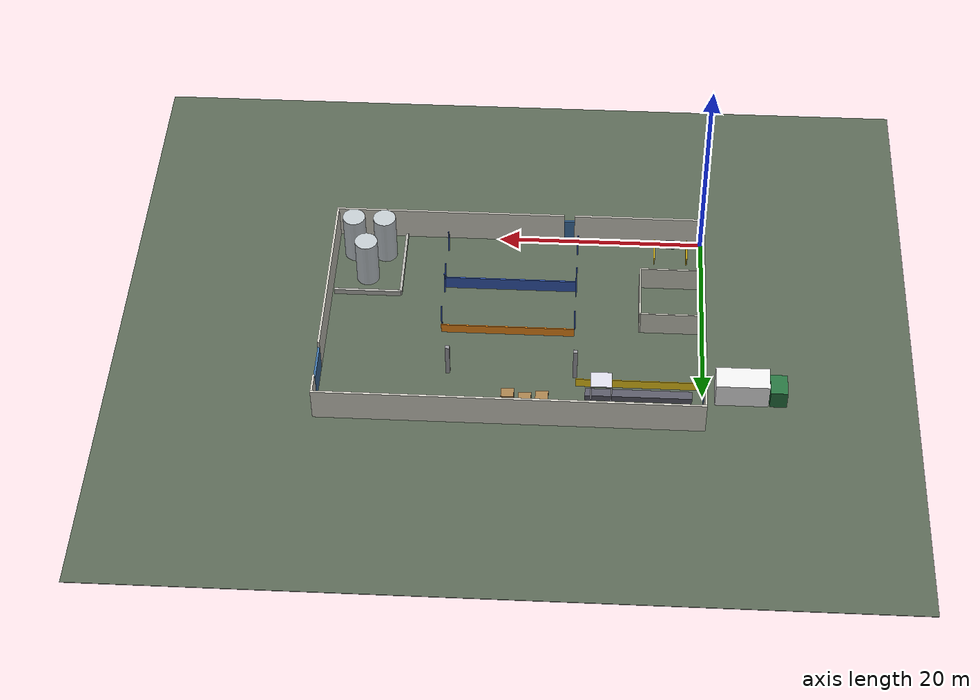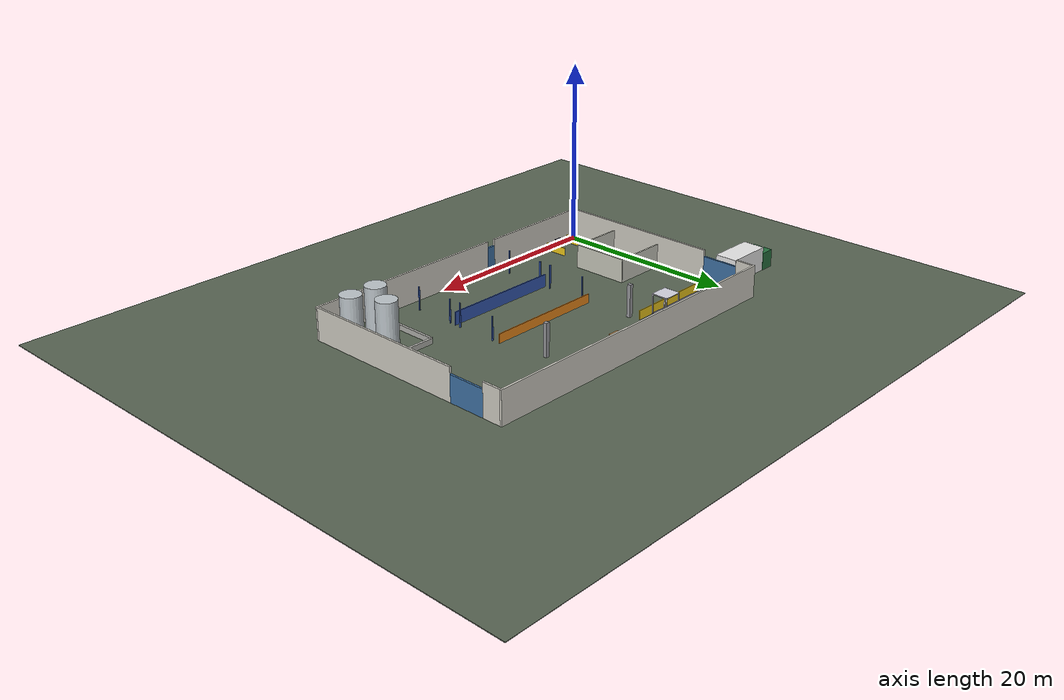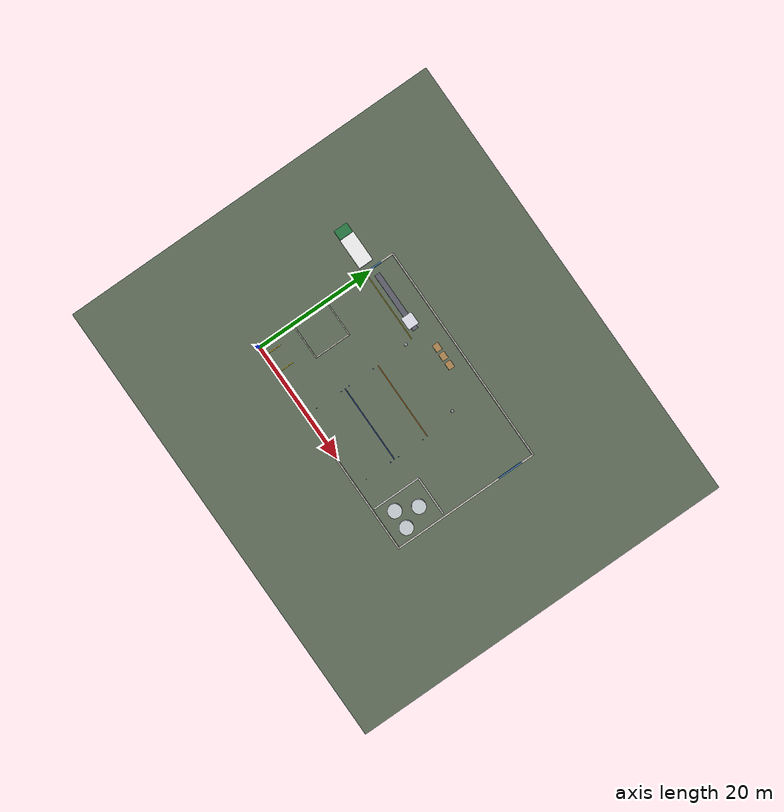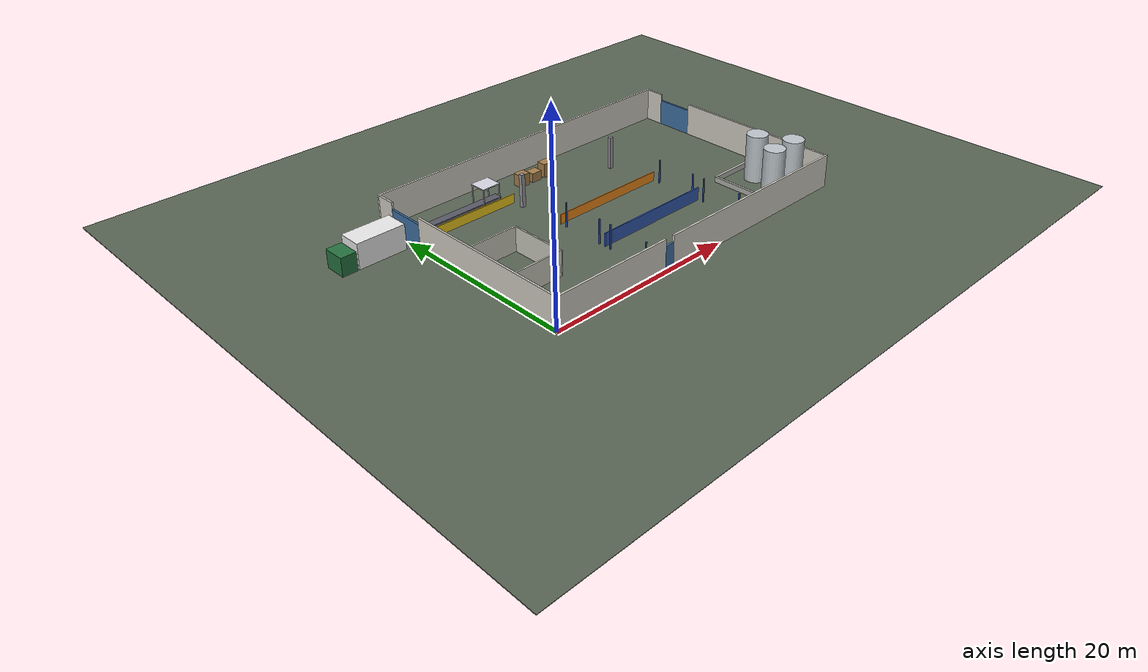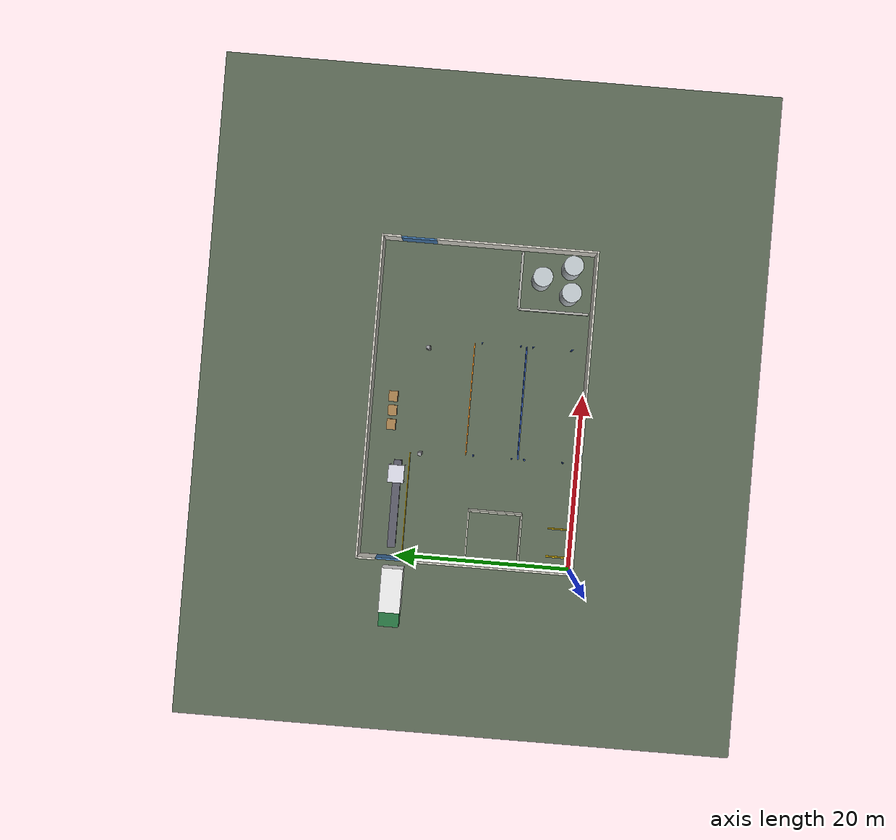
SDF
<?xml version="1.0"?>
<!-- GENERATED by uco_simulation/scripts/generate_world.py from warehouse_layout.yaml.
     Do not edit by hand: change the layout YAML and regenerate. -->
<sdf version="1.9">
  <world name="uco_warehouse">
    <physics name="default_physics" type="ignored">
      <max_step_size>0.002</max_step_size>
      <real_time_factor>1.0</real_time_factor>
      <real_time_update_rate>500</real_time_update_rate>
    </physics>
    <plugin filename="gz-sim-physics-system" name="gz::sim::systems::Physics"/>
    <plugin filename="gz-sim-user-commands-system" name="gz::sim::systems::UserCommands"/>
    <plugin filename="gz-sim-scene-broadcaster-system" name="gz::sim::systems::SceneBroadcaster"/>
    <plugin filename="gz-sim-sensors-system" name="gz::sim::systems::Sensors">
      <render_engine>ogre2</render_engine>
    </plugin>
    <plugin filename="gz-sim-imu-system" name="gz::sim::systems::Imu"/>
    <gravity>0 0 -9.81</gravity>
    <scene>
      <ambient>0.55 0.55 0.55 1</ambient>
      <background>0.7 0.78 0.85 1</background>
      <shadows>false</shadows>
      <grid>false</grid>
    </scene>
    <light type="directional" name="sun">
      <cast_shadows>false</cast_shadows>
      <pose>0 0 20 0 0 0</pose>
      <diffuse>0.7 0.7 0.68 1</diffuse>
      <specular>0.2 0.2 0.2 1</specular>
      <direction>-0.4 0.3 -0.85</direction>
    </light>
    <light type="point" name="ceiling_light_0"><pose>7.2 7.2 3.2 0 0 0</pose><diffuse>0.55 0.55 0.52 1</diffuse><specular>0.1 0.1 0.1 1</specular><attenuation><range>25</range><constant>0.6</constant><linear>0.02</linear><quadratic>0.001</quadratic></attenuation><cast_shadows>false</cast_shadows></light><light type="point" name="ceiling_light_1"><pose>18.0 7.2 3.2 0 0 0</pose><diffuse>0.55 0.55 0.52 1</diffuse><specular>0.1 0.1 0.1 1</specular><attenuation><range>25</range><constant>0.6</constant><linear>0.02</linear><quadratic>0.001</quadratic></attenuation><cast_shadows>false</cast_shadows></light><light type="point" name="ceiling_light_2"><pose>28.8 7.2 3.2 0 0 0</pose><diffuse>0.55 0.55 0.52 1</diffuse><specular>0.1 0.1 0.1 1</specular><attenuation><range>25</range><constant>0.6</constant><linear>0.02</linear><quadratic>0.001</quadratic></attenuation><cast_shadows>false</cast_shadows></light><light type="point" name="ceiling_light_3"><pose>7.2 18.0 3.2 0 0 0</pose><diffuse>0.55 0.55 0.52 1</diffuse><specular>0.1 0.1 0.1 1</specular><attenuation><range>25</range><constant>0.6</constant><linear>0.02</linear><quadratic>0.001</quadratic></attenuation><cast_shadows>false</cast_shadows></light><light type="point" name="ceiling_light_4"><pose>18.0 18.0 3.2 0 0 0</pose><diffuse>0.55 0.55 0.52 1</diffuse><specular>0.1 0.1 0.1 1</specular><attenuation><range>25</range><constant>0.6</constant><linear>0.02</linear><quadratic>0.001</quadratic></attenuation><cast_shadows>false</cast_shadows></light><light type="point" name="ceiling_light_5"><pose>28.8 18.0 3.2 0 0 0</pose><diffuse>0.55 0.55 0.52 1</diffuse><specular>0.1 0.1 0.1 1</specular><attenuation><range>25</range><constant>0.6</constant><linear>0.02</linear><quadratic>0.001</quadratic></attenuation><cast_shadows>false</cast_shadows></light>
    <model name="floor"><static>true</static><link name="link"><collision name="c"><geometry><plane><normal>0 0 1</normal><size>76.0 64.0</size></plane></geometry><surface><friction><ode><mu>1.0</mu><mu2>1.0</mu2></ode></friction></surface></collision><visual name="concrete"><pose>18.00 12.00 0 0 0 0</pose><geometry><plane><normal>0 0 1</normal><size>36.40 24.40</size></plane></geometry><material><ambient>0.62 0.63 0.62 1</ambient><diffuse>0.62 0.63 0.62 1</diffuse></material></visual><visual name="yard"><pose>18.00 12.00 -0.01 0 0 0</pose><geometry><plane><normal>0 0 1</normal><size>76.0 64.0</size></plane></geometry><material><ambient>0.350 0.400 0.330 1</ambient><diffuse>0.350 0.400 0.330 1</diffuse></material></visual></link></model>
    <model name="wall_south_0"><static>true</static><pose>6.200 -0.100 1.750 0 0 0.0000</pose><link name="link"><collision name="c"><geometry><box><size>12.800 0.200 3.500</size></box></geometry></collision><visual name="v"><geometry><box><size>12.800 0.200 3.500</size></box></geometry><material><ambient>0.83 0.82 0.78 1</ambient><diffuse>0.83 0.82 0.78 1</diffuse></material></visual></link></model><model name="wall_south_1"><static>true</static><pose>24.900 -0.100 1.750 0 0 0.0000</pose><link name="link"><collision name="c"><geometry><box><size>22.600 0.200 3.500</size></box></geometry></collision><visual name="v"><geometry><box><size>22.600 0.200 3.500</size></box></geometry><material><ambient>0.83 0.82 0.78 1</ambient><diffuse>0.83 0.82 0.78 1</diffuse></material></visual></link></model><model name="wall_north_0"><static>true</static><pose>18.000 24.100 1.750 0 0 0.0000</pose><link name="link"><collision name="c"><geometry><box><size>36.400 0.200 3.500</size></box></geometry></collision><visual name="v"><geometry><box><size>36.400 0.200 3.500</size></box></geometry><material><ambient>0.83 0.82 0.78 1</ambient><diffuse>0.83 0.82 0.78 1</diffuse></material></visual></link></model><model name="wall_west_0"><static>true</static><pose>-0.100 9.000 1.750 0 0 0.0000</pose><link name="link"><collision name="c"><geometry><box><size>0.200 18.000 3.500</size></box></geometry></collision><visual name="v"><geometry><box><size>0.200 18.000 3.500</size></box></geometry><material><ambient>0.83 0.82 0.78 1</ambient><diffuse>0.83 0.82 0.78 1</diffuse></material></visual></link></model><model name="wall_west_1"><static>true</static><pose>-0.100 23.000 1.750 0 0 0.0000</pose><link name="link"><collision name="c"><geometry><box><size>0.200 2.000 3.500</size></box></geometry></collision><visual name="v"><geometry><box><size>0.200 2.000 3.500</size></box></geometry><material><ambient>0.83 0.82 0.78 1</ambient><diffuse>0.83 0.82 0.78 1</diffuse></material></visual></link></model><model name="wall_east_0"><static>true</static><pose>36.100 9.000 1.750 0 0 0.0000</pose><link name="link"><collision name="c"><geometry><box><size>0.200 18.000 3.500</size></box></geometry></collision><visual name="v"><geometry><box><size>0.200 18.000 3.500</size></box></geometry><material><ambient>0.83 0.82 0.78 1</ambient><diffuse>0.83 0.82 0.78 1</diffuse></material></visual></link></model><model name="wall_east_1"><static>true</static><pose>36.100 23.000 1.750 0 0 0.0000</pose><link name="link"><collision name="c"><geometry><box><size>0.200 2.000 3.500</size></box></geometry></collision><visual name="v"><geometry><box><size>0.200 2.000 3.500</size></box></geometry><material><ambient>0.83 0.82 0.78 1</ambient><diffuse>0.83 0.82 0.78 1</diffuse></material></visual></link></model><model name="personnel_door"><static>true</static><pose>13.100 -0.100 1.400 0 0 0.0000</pose><link name="link"><collision name="c"><geometry><box><size>1.000 0.200 2.800</size></box></geometry></collision><visual name="v"><geometry><box><size>1.000 0.200 2.800</size></box></geometry><material><ambient>0.25 0.45 0.65 1</ambient><diffuse>0.25 0.45 0.65 1</diffuse></material></visual></link></model><model name="dock_door"><static>true</static><pose>-0.100 20.000 1.400 0 0 0.0000</pose><link name="link"><collision name="c"><geometry><box><size>0.200 4.000 2.800</size></box></geometry></collision><visual name="v"><geometry><box><size>0.200 4.000 2.800</size></box></geometry><material><ambient>0.25 0.45 0.65 1</ambient><diffuse>0.25 0.45 0.65 1</diffuse></material></visual></link></model><model name="dispatch_door"><static>true</static><pose>36.100 20.000 1.400 0 0 0.0000</pose><link name="link"><collision name="c"><geometry><box><size>0.200 4.000 2.800</size></box></geometry></collision><visual name="v"><geometry><box><size>0.200 4.000 2.800</size></box></geometry><material><ambient>0.25 0.45 0.65 1</ambient><diffuse>0.25 0.45 0.65 1</diffuse></material></visual></link></model><model name="conveyor"><static>true</static><pose>6.000 20.500 0.350 0 0 0.0000</pose><link name="link"><collision name="c"><geometry><box><size>10.000 0.900 0.700</size></box></geometry></collision><visual name="v"><geometry><box><size>10.000 0.900 0.700</size></box></geometry><material><ambient>0.350 0.350 0.400 1</ambient><diffuse>0.350 0.350 0.400 1</diffuse></material></visual></link></model><model name="inspection_booth_roof"><static>true</static><pose>9.500 20.500 2.450 0 0 0.0000</pose><link name="link"><visual name="v"><geometry><box><size>2.000 1.800 0.100</size></box></geometry><material><ambient>0.850 0.850 0.900 1</ambient><diffuse>0.850 0.850 0.900 1</diffuse></material></visual></link></model><model name="inspection_post_1"><static>true</static><pose>8.550 19.650 1.200 0 0 0.0000</pose><link name="link"><collision name="c"><geometry><box><size>0.100 0.100 2.400</size></box></geometry></collision><visual name="v"><geometry><box><size>0.100 0.100 2.400</size></box></geometry><material><ambient>0.850 0.850 0.900 1</ambient><diffuse>0.850 0.850 0.900 1</diffuse></material></visual></link></model><model name="inspection_post_2"><static>true</static><pose>10.450 19.650 1.200 0 0 0.0000</pose><link name="link"><collision name="c"><geometry><box><size>0.100 0.100 2.400</size></box></geometry></collision><visual name="v"><geometry><box><size>0.100 0.100 2.400</size></box></geometry><material><ambient>0.850 0.850 0.900 1</ambient><diffuse>0.850 0.850 0.900 1</diffuse></material></visual></link></model><model name="inspection_post_3"><static>true</static><pose>8.550 21.350 1.200 0 0 0.0000</pose><link name="link"><collision name="c"><geometry><box><size>0.100 0.100 2.400</size></box></geometry></collision><visual name="v"><geometry><box><size>0.100 0.100 2.400</size></box></geometry><material><ambient>0.850 0.850 0.900 1</ambient><diffuse>0.850 0.850 0.900 1</diffuse></material></visual></link></model><model name="inspection_post_4"><static>true</static><pose>10.450 21.350 1.200 0 0 0.0000</pose><link name="link"><collision name="c"><geometry><box><size>0.100 0.100 2.400</size></box></geometry></collision><visual name="v"><geometry><box><size>0.100 0.100 2.400</size></box></geometry><material><ambient>0.850 0.850 0.900 1</ambient><diffuse>0.850 0.850 0.900 1</diffuse></material></visual></link></model><model name="receiving_barrier"><static>true</static><pose>6.100 19.200 0.500 0 0 0.0000</pose><link name="link"><collision name="c"><geometry><box><size>11.600 0.080 1.000</size></box></geometry></collision><visual name="v"><geometry><box><size>11.600 0.080 1.000</size></box></geometry><material><ambient>0.950 0.800 0.100 1</ambient><diffuse>0.950 0.800 0.100 1</diffuse></material></visual></link></model><model name="office_wall_s"><static>true</static><pose>3.100 6.000 1.300 0 0 0.0000</pose><link name="link"><collision name="c"><geometry><box><size>5.800 0.150 2.600</size></box></geometry></collision><visual name="v"><geometry><box><size>5.800 0.150 2.600</size></box></geometry><material><ambient>0.800 0.800 0.750 1</ambient><diffuse>0.800 0.800 0.750 1</diffuse></material></visual></link></model><model name="office_wall_n"><static>true</static><pose>3.100 12.000 1.300 0 0 0.0000</pose><link name="link"><collision name="c"><geometry><box><size>5.800 0.150 2.600</size></box></geometry></collision><visual name="v"><geometry><box><size>5.800 0.150 2.600</size></box></geometry><material><ambient>0.800 0.800 0.750 1</ambient><diffuse>0.800 0.800 0.750 1</diffuse></material></visual></link></model><model name="office_wall_e"><static>true</static><pose>6.000 9.000 1.300 0 0 0.0000</pose><link name="link"><collision name="c"><geometry><box><size>0.150 6.150 2.600</size></box></geometry></collision><visual name="v"><geometry><box><size>0.150 6.150 2.600</size></box></geometry><material><ambient>0.800 0.800 0.750 1</ambient><diffuse>0.800 0.800 0.750 1</diffuse></material></visual></link></model><model name="rack_guard_rail_north"><static>true</static><pose>18.600 12.850 0.500 0 0 0.0000</pose><link name="link"><collision name="c"><geometry><box><size>12.800 0.100 1.000</size></box></geometry></collision><visual name="v"><geometry><box><size>12.800 0.100 1.000</size></box></geometry><material><ambient>0.950 0.550 0.100 1</ambient><diffuse>0.950 0.550 0.100 1</diffuse></material></visual></link></model><model name="rack_spine"><static>true</static><pose>18.600 6.900 0.700 0 0 0.0000</pose><link name="link"><collision name="c"><geometry><box><size>12.800 0.120 1.400</size></box></geometry></collision><visual name="v"><geometry><box><size>12.800 0.120 1.400</size></box></geometry><material><ambient>0.200 0.350 0.700 1</ambient><diffuse>0.200 0.350 0.700 1</diffuse></material></visual></link></model><model name="rack_post_a1w"><static>true</static><pose>12.200 12.000 1.300 0 0 0.0000</pose><link name="link"><collision name="c"><geometry><box><size>0.120 0.120 2.600</size></box></geometry></collision><visual name="v"><geometry><box><size>0.120 0.120 2.600</size></box></geometry><material><ambient>0.200 0.350 0.700 1</ambient><diffuse>0.200 0.350 0.700 1</diffuse></material></visual></link></model><model name="rack_post_a1e"><static>true</static><pose>25.000 12.000 1.300 0 0 0.0000</pose><link name="link"><collision name="c"><geometry><box><size>0.120 0.120 2.600</size></box></geometry></collision><visual name="v"><geometry><box><size>0.120 0.120 2.600</size></box></geometry><material><ambient>0.200 0.350 0.700 1</ambient><diffuse>0.200 0.350 0.700 1</diffuse></material></visual></link></model><model name="rack_post_a2w"><static>true</static><pose>12.200 7.600 1.300 0 0 0.0000</pose><link name="link"><collision name="c"><geometry><box><size>0.120 0.120 2.600</size></box></geometry></collision><visual name="v"><geometry><box><size>0.120 0.120 2.600</size></box></geometry><material><ambient>0.200 0.350 0.700 1</ambient><diffuse>0.200 0.350 0.700 1</diffuse></material></visual></link></model><model name="rack_post_a2e"><static>true</static><pose>25.000 7.600 1.300 0 0 0.0000</pose><link name="link"><collision name="c"><geometry><box><size>0.120 0.120 2.600</size></box></geometry></collision><visual name="v"><geometry><box><size>0.120 0.120 2.600</size></box></geometry><material><ambient>0.200 0.350 0.700 1</ambient><diffuse>0.200 0.350 0.700 1</diffuse></material></visual></link></model><model name="rack_post_b1w"><static>true</static><pose>12.200 6.200 1.300 0 0 0.0000</pose><link name="link"><collision name="c"><geometry><box><size>0.120 0.120 2.600</size></box></geometry></collision><visual name="v"><geometry><box><size>0.120 0.120 2.600</size></box></geometry><material><ambient>0.200 0.350 0.700 1</ambient><diffuse>0.200 0.350 0.700 1</diffuse></material></visual></link></model><model name="rack_post_b1e"><static>true</static><pose>25.000 6.200 1.300 0 0 0.0000</pose><link name="link"><collision name="c"><geometry><box><size>0.120 0.120 2.600</size></box></geometry></collision><visual name="v"><geometry><box><size>0.120 0.120 2.600</size></box></geometry><material><ambient>0.200 0.350 0.700 1</ambient><diffuse>0.200 0.350 0.700 1</diffuse></material></visual></link></model><model name="rack_post_b2w"><static>true</static><pose>12.200 1.800 1.300 0 0 0.0000</pose><link name="link"><collision name="c"><geometry><box><size>0.120 0.120 2.600</size></box></geometry></collision><visual name="v"><geometry><box><size>0.120 0.120 2.600</size></box></geometry><material><ambient>0.200 0.350 0.700 1</ambient><diffuse>0.200 0.350 0.700 1</diffuse></material></visual></link></model><model name="rack_post_b2e"><static>true</static><pose>25.000 1.800 1.300 0 0 0.0000</pose><link name="link"><collision name="c"><geometry><box><size>0.120 0.120 2.600</size></box></geometry></collision><visual name="v"><geometry><box><size>0.120 0.120 2.600</size></box></geometry><material><ambient>0.200 0.350 0.700 1</ambient><diffuse>0.200 0.350 0.700 1</diffuse></material></visual></link></model><model name="bund_n"><static>true</static><pose>32.550 8.200 0.300 0 0 0.0000</pose><link name="link"><collision name="c"><geometry><box><size>6.500 0.250 0.600</size></box></geometry></collision><visual name="v"><geometry><box><size>6.500 0.250 0.600</size></box></geometry><material><ambient>0.700 0.700 0.680 1</ambient><diffuse>0.700 0.700 0.680 1</diffuse></material></visual></link></model><model name="bund_w"><static>true</static><pose>29.300 4.200 0.300 0 0 0.0000</pose><link name="link"><collision name="c"><geometry><box><size>0.250 8.000 0.600</size></box></geometry></collision><visual name="v"><geometry><box><size>0.250 8.000 0.600</size></box></geometry><material><ambient>0.700 0.700 0.680 1</ambient><diffuse>0.700 0.700 0.680 1</diffuse></material></visual></link></model><model name="tank_1"><static>true</static><pose>31.200 2.600 2.500 0 0 0</pose><link name="link"><collision name="c"><geometry><cylinder><radius>1.100</radius><length>5.000</length></cylinder></geometry></collision><visual name="v"><geometry><cylinder><radius>1.100</radius><length>5.000</length></cylinder></geometry><material><ambient>0.750 0.780 0.800 1</ambient><diffuse>0.750 0.780 0.800 1</diffuse></material></visual></link></model><model name="tank_2"><static>true</static><pose>34.200 2.600 2.500 0 0 0</pose><link name="link"><collision name="c"><geometry><cylinder><radius>1.100</radius><length>5.000</length></cylinder></geometry></collision><visual name="v"><geometry><cylinder><radius>1.100</radius><length>5.000</length></cylinder></geometry><material><ambient>0.750 0.780 0.800 1</ambient><diffuse>0.750 0.780 0.800 1</diffuse></material></visual></link></model><model name="tank_3"><static>true</static><pose>32.700 5.900 2.500 0 0 0</pose><link name="link"><collision name="c"><geometry><cylinder><radius>1.100</radius><length>5.000</length></cylinder></geometry></collision><visual name="v"><geometry><cylinder><radius>1.100</radius><length>5.000</length></cylinder></geometry><material><ambient>0.750 0.780 0.800 1</ambient><diffuse>0.750 0.780 0.800 1</diffuse></material></visual></link></model><model name="charger_unit"><static>true</static><pose>3.000 0.400 0.450 0 0 0.0000</pose><link name="link"><collision name="c"><geometry><box><size>0.800 0.350 0.900</size></box></geometry></collision><visual name="v"><geometry><box><size>0.800 0.350 0.900</size></box></geometry><material><ambient>0.250 0.250 0.300 1</ambient><diffuse>0.250 0.250 0.300 1</diffuse></material></visual></link></model><model name="charger_barrier_w"><static>true</static><pose>1.400 1.500 0.450 0 0 0.0000</pose><link name="link"><collision name="c"><geometry><box><size>0.100 2.600 0.900</size></box></geometry></collision><visual name="v"><geometry><box><size>0.100 2.600 0.900</size></box></geometry><material><ambient>0.950 0.800 0.100 1</ambient><diffuse>0.950 0.800 0.100 1</diffuse></material></visual></link></model><model name="charger_barrier_e"><static>true</static><pose>4.600 1.500 0.450 0 0 0.0000</pose><link name="link"><collision name="c"><geometry><box><size>0.100 2.600 0.900</size></box></geometry></collision><visual name="v"><geometry><box><size>0.100 2.600 0.900</size></box></geometry><material><ambient>0.950 0.800 0.100 1</ambient><diffuse>0.950 0.800 0.100 1</diffuse></material></visual></link></model><model name="pallet_stack_1"><static>true</static><pose>15.000 21.600 0.650 0 0 0.0000</pose><link name="link"><collision name="c"><geometry><box><size>1.200 1.000 1.300</size></box></geometry></collision><visual name="v"><geometry><box><size>1.200 1.000 1.300</size></box></geometry><material><ambient>0.650 0.500 0.300 1</ambient><diffuse>0.650 0.500 0.300 1</diffuse></material></visual></link></model><model name="pallet_stack_2"><static>true</static><pose>16.600 21.600 0.500 0 0 0.0000</pose><link name="link"><collision name="c"><geometry><box><size>1.200 1.000 1.000</size></box></geometry></collision><visual name="v"><geometry><box><size>1.200 1.000 1.000</size></box></geometry><material><ambient>0.650 0.500 0.300 1</ambient><diffuse>0.650 0.500 0.300 1</diffuse></material></visual></link></model><model name="pallet_stack_3"><static>true</static><pose>18.200 21.600 0.750 0 0 0.0000</pose><link name="link"><collision name="c"><geometry><box><size>1.200 1.000 1.500</size></box></geometry></collision><visual name="v"><geometry><box><size>1.200 1.000 1.500</size></box></geometry><material><ambient>0.650 0.500 0.300 1</ambient><diffuse>0.650 0.500 0.300 1</diffuse></material></visual></link></model><model name="column_1"><static>true</static><pose>12.000 18.000 1.750 0 0 0.0000</pose><link name="link"><collision name="c"><geometry><box><size>0.400 0.400 3.500</size></box></geometry></collision><visual name="v"><geometry><box><size>0.400 0.400 3.500</size></box></geometry><material><ambient>0.600 0.600 0.620 1</ambient><diffuse>0.600 0.600 0.620 1</diffuse></material></visual></link></model><model name="column_2"><static>true</static><pose>24.000 18.000 1.750 0 0 0.0000</pose><link name="link"><collision name="c"><geometry><box><size>0.400 0.400 3.500</size></box></geometry></collision><visual name="v"><geometry><box><size>0.400 0.400 3.500</size></box></geometry><material><ambient>0.600 0.600 0.620 1</ambient><diffuse>0.600 0.600 0.620 1</diffuse></material></visual></link></model><model name="floor_markings"><static>true</static><link name="link"><visual name="zone_receiving_s"><pose>6.100 13.060 0.002 0 0 0</pose><geometry><box><size>11.800 0.120 0.002</size></box></geometry><material><ambient>0.950 0.750 0.200 1</ambient><diffuse>0.950 0.750 0.200 1</diffuse></material></visual><visual name="zone_receiving_n"><pose>6.100 19.140 0.002 0 0 0</pose><geometry><box><size>11.800 0.120 0.002</size></box></geometry><material><ambient>0.950 0.750 0.200 1</ambient><diffuse>0.950 0.750 0.200 1</diffuse></material></visual><visual name="zone_receiving_w"><pose>0.260 16.100 0.002 0 0 0</pose><geometry><box><size>0.120 6.200 0.002</size></box></geometry><material><ambient>0.950 0.750 0.200 1</ambient><diffuse>0.950 0.750 0.200 1</diffuse></material></visual><visual name="zone_receiving_e"><pose>11.940 16.100 0.002 0 0 0</pose><geometry><box><size>0.120 6.200 0.002</size></box></geometry><material><ambient>0.950 0.750 0.200 1</ambient><diffuse>0.950 0.750 0.200 1</diffuse></material></visual><visual name="zone_receiving_process_s"><pose>6.100 19.260 0.002 0 0 0</pose><geometry><box><size>11.800 0.120 0.002</size></box></geometry><material><ambient>0.900 0.300 0.200 1</ambient><diffuse>0.900 0.300 0.200 1</diffuse></material></visual><visual name="zone_receiving_process_n"><pose>6.100 23.740 0.002 0 0 0</pose><geometry><box><size>11.800 0.120 0.002</size></box></geometry><material><ambient>0.900 0.300 0.200 1</ambient><diffuse>0.900 0.300 0.200 1</diffuse></material></visual><visual name="zone_receiving_process_w"><pose>0.260 21.500 0.002 0 0 0</pose><geometry><box><size>0.120 4.600 0.002</size></box></geometry><material><ambient>0.900 0.300 0.200 1</ambient><diffuse>0.900 0.300 0.200 1</diffuse></material></visual><visual name="zone_receiving_process_e"><pose>11.940 21.500 0.002 0 0 0</pose><geometry><box><size>0.120 4.600 0.002</size></box></geometry><material><ambient>0.900 0.300 0.200 1</ambient><diffuse>0.900 0.300 0.200 1</diffuse></material></visual><visual name="hatch_receiving_process_0"><pose>0.621 21.500 0.002 0 0 0</pose><geometry><box><size>0.150 4.300 0.002</size></box></geometry><material><ambient>0.850 0.250 0.200 1</ambient><diffuse>0.850 0.250 0.200 1</diffuse></material></visual><visual name="hatch_receiving_process_1"><pose>1.464 21.500 0.002 0 0 0</pose><geometry><box><size>0.150 4.300 0.002</size></box></geometry><material><ambient>0.850 0.250 0.200 1</ambient><diffuse>0.850 0.250 0.200 1</diffuse></material></visual><visual name="hatch_receiving_process_2"><pose>2.307 21.500 0.002 0 0 0</pose><geometry><box><size>0.150 4.300 0.002</size></box></geometry><material><ambient>0.850 0.250 0.200 1</ambient><diffuse>0.850 0.250 0.200 1</diffuse></material></visual><visual name="hatch_receiving_process_3"><pose>3.150 21.500 0.002 0 0 0</pose><geometry><box><size>0.150 4.300 0.002</size></box></geometry><material><ambient>0.850 0.250 0.200 1</ambient><diffuse>0.850 0.250 0.200 1</diffuse></material></visual><visual name="hatch_receiving_process_4"><pose>3.993 21.500 0.002 0 0 0</pose><geometry><box><size>0.150 4.300 0.002</size></box></geometry><material><ambient>0.850 0.250 0.200 1</ambient><diffuse>0.850 0.250 0.200 1</diffuse></material></visual><visual name="hatch_receiving_process_5"><pose>4.836 21.500 0.002 0 0 0</pose><geometry><box><size>0.150 4.300 0.002</size></box></geometry><material><ambient>0.850 0.250 0.200 1</ambient><diffuse>0.850 0.250 0.200 1</diffuse></material></visual><visual name="hatch_receiving_process_6"><pose>5.679 21.500 0.002 0 0 0</pose><geometry><box><size>0.150 4.300 0.002</size></box></geometry><material><ambient>0.850 0.250 0.200 1</ambient><diffuse>0.850 0.250 0.200 1</diffuse></material></visual><visual name="hatch_receiving_process_7"><pose>6.521 21.500 0.002 0 0 0</pose><geometry><box><size>0.150 4.300 0.002</size></box></geometry><material><ambient>0.850 0.250 0.200 1</ambient><diffuse>0.850 0.250 0.200 1</diffuse></material></visual><visual name="hatch_receiving_process_8"><pose>7.364 21.500 0.002 0 0 0</pose><geometry><box><size>0.150 4.300 0.002</size></box></geometry><material><ambient>0.850 0.250 0.200 1</ambient><diffuse>0.850 0.250 0.200 1</diffuse></material></visual><visual name="hatch_receiving_process_9"><pose>8.207 21.500 0.002 0 0 0</pose><geometry><box><size>0.150 4.300 0.002</size></box></geometry><material><ambient>0.850 0.250 0.200 1</ambient><diffuse>0.850 0.250 0.200 1</diffuse></material></visual><visual name="hatch_receiving_process_10"><pose>9.050 21.500 0.002 0 0 0</pose><geometry><box><size>0.150 4.300 0.002</size></box></geometry><material><ambient>0.850 0.250 0.200 1</ambient><diffuse>0.850 0.250 0.200 1</diffuse></material></visual><visual name="hatch_receiving_process_11"><pose>9.893 21.500 0.002 0 0 0</pose><geometry><box><size>0.150 4.300 0.002</size></box></geometry><material><ambient>0.850 0.250 0.200 1</ambient><diffuse>0.850 0.250 0.200 1</diffuse></material></visual><visual name="hatch_receiving_process_12"><pose>10.736 21.500 0.002 0 0 0</pose><geometry><box><size>0.150 4.300 0.002</size></box></geometry><material><ambient>0.850 0.250 0.200 1</ambient><diffuse>0.850 0.250 0.200 1</diffuse></material></visual><visual name="hatch_receiving_process_13"><pose>11.579 21.500 0.002 0 0 0</pose><geometry><box><size>0.150 4.300 0.002</size></box></geometry><material><ambient>0.850 0.250 0.200 1</ambient><diffuse>0.850 0.250 0.200 1</diffuse></material></visual><visual name="zone_storage_s"><pose>18.700 0.260 0.002 0 0 0</pose><geometry><box><size>13.000 0.120 0.002</size></box></geometry><material><ambient>0.300 0.600 0.950 1</ambient><diffuse>0.300 0.600 0.950 1</diffuse></material></visual><visual name="zone_storage_n"><pose>18.700 12.740 0.002 0 0 0</pose><geometry><box><size>13.000 0.120 0.002</size></box></geometry><material><ambient>0.300 0.600 0.950 1</ambient><diffuse>0.300 0.600 0.950 1</diffuse></material></visual><visual name="zone_storage_w"><pose>12.260 6.500 0.002 0 0 0</pose><geometry><box><size>0.120 12.600 0.002</size></box></geometry><material><ambient>0.300 0.600 0.950 1</ambient><diffuse>0.300 0.600 0.950 1</diffuse></material></visual><visual name="zone_storage_e"><pose>25.140 6.500 0.002 0 0 0</pose><geometry><box><size>0.120 12.600 0.002</size></box></geometry><material><ambient>0.300 0.600 0.950 1</ambient><diffuse>0.300 0.600 0.950 1</diffuse></material></visual><visual name="zone_dispatch_s"><pose>32.400 8.660 0.002 0 0 0</pose><geometry><box><size>6.800 0.120 0.002</size></box></geometry><material><ambient>0.300 0.850 0.400 1</ambient><diffuse>0.300 0.850 0.400 1</diffuse></material></visual><visual name="zone_dispatch_n"><pose>32.400 23.740 0.002 0 0 0</pose><geometry><box><size>6.800 0.120 0.002</size></box></geometry><material><ambient>0.300 0.850 0.400 1</ambient><diffuse>0.300 0.850 0.400 1</diffuse></material></visual><visual name="zone_dispatch_w"><pose>29.060 16.200 0.002 0 0 0</pose><geometry><box><size>0.120 15.200 0.002</size></box></geometry><material><ambient>0.300 0.850 0.400 1</ambient><diffuse>0.300 0.850 0.400 1</diffuse></material></visual><visual name="zone_dispatch_e"><pose>35.740 16.200 0.002 0 0 0</pose><geometry><box><size>0.120 15.200 0.002</size></box></geometry><material><ambient>0.300 0.850 0.400 1</ambient><diffuse>0.300 0.850 0.400 1</diffuse></material></visual><visual name="zone_charging_s"><pose>3.000 0.260 0.002 0 0 0</pose><geometry><box><size>3.200 0.120 0.002</size></box></geometry><material><ambient>0.600 0.400 0.900 1</ambient><diffuse>0.600 0.400 0.900 1</diffuse></material></visual><visual name="zone_charging_n"><pose>3.000 2.940 0.002 0 0 0</pose><geometry><box><size>3.200 0.120 0.002</size></box></geometry><material><ambient>0.600 0.400 0.900 1</ambient><diffuse>0.600 0.400 0.900 1</diffuse></material></visual><visual name="zone_charging_w"><pose>1.460 1.600 0.002 0 0 0</pose><geometry><box><size>0.120 2.800 0.002</size></box></geometry><material><ambient>0.600 0.400 0.900 1</ambient><diffuse>0.600 0.400 0.900 1</diffuse></material></visual><visual name="zone_charging_e"><pose>4.540 1.600 0.002 0 0 0</pose><geometry><box><size>0.120 2.800 0.002</size></box></geometry><material><ambient>0.600 0.400 0.900 1</ambient><diffuse>0.600 0.400 0.900 1</diffuse></material></visual><visual name="zone_quarantine_s"><pose>8.800 0.260 0.002 0 0 0</pose><geometry><box><size>5.200 0.120 0.002</size></box></geometry><material><ambient>0.950 0.500 0.100 1</ambient><diffuse>0.950 0.500 0.100 1</diffuse></material></visual><visual name="zone_quarantine_n"><pose>8.800 2.140 0.002 0 0 0</pose><geometry><box><size>5.200 0.120 0.002</size></box></geometry><material><ambient>0.950 0.500 0.100 1</ambient><diffuse>0.950 0.500 0.100 1</diffuse></material></visual><visual name="zone_quarantine_w"><pose>6.260 1.200 0.002 0 0 0</pose><geometry><box><size>0.120 2.000 0.002</size></box></geometry><material><ambient>0.950 0.500 0.100 1</ambient><diffuse>0.950 0.500 0.100 1</diffuse></material></visual><visual name="zone_quarantine_e"><pose>11.340 1.200 0.002 0 0 0</pose><geometry><box><size>0.120 2.000 0.002</size></box></geometry><material><ambient>0.950 0.500 0.100 1</ambient><diffuse>0.950 0.500 0.100 1</diffuse></material></visual><visual name="zone_tank_farm_s"><pose>32.550 0.260 0.002 0 0 0</pose><geometry><box><size>6.500 0.120 0.002</size></box></geometry><material><ambient>0.900 0.300 0.200 1</ambient><diffuse>0.900 0.300 0.200 1</diffuse></material></visual><visual name="zone_tank_farm_n"><pose>32.550 8.140 0.002 0 0 0</pose><geometry><box><size>6.500 0.120 0.002</size></box></geometry><material><ambient>0.900 0.300 0.200 1</ambient><diffuse>0.900 0.300 0.200 1</diffuse></material></visual><visual name="zone_tank_farm_w"><pose>29.360 4.200 0.002 0 0 0</pose><geometry><box><size>0.120 8.000 0.002</size></box></geometry><material><ambient>0.900 0.300 0.200 1</ambient><diffuse>0.900 0.300 0.200 1</diffuse></material></visual><visual name="zone_tank_farm_e"><pose>35.740 4.200 0.002 0 0 0</pose><geometry><box><size>0.120 8.000 0.002</size></box></geometry><material><ambient>0.900 0.300 0.200 1</ambient><diffuse>0.900 0.300 0.200 1</diffuse></material></visual><visual name="hatch_tank_farm_0"><pose>29.706 4.200 0.002 0 0 0</pose><geometry><box><size>0.150 7.700 0.002</size></box></geometry><material><ambient>0.850 0.250 0.200 1</ambient><diffuse>0.850 0.250 0.200 1</diffuse></material></visual><visual name="hatch_tank_farm_1"><pose>30.519 4.200 0.002 0 0 0</pose><geometry><box><size>0.150 7.700 0.002</size></box></geometry><material><ambient>0.850 0.250 0.200 1</ambient><diffuse>0.850 0.250 0.200 1</diffuse></material></visual><visual name="hatch_tank_farm_2"><pose>31.331 4.200 0.002 0 0 0</pose><geometry><box><size>0.150 7.700 0.002</size></box></geometry><material><ambient>0.850 0.250 0.200 1</ambient><diffuse>0.850 0.250 0.200 1</diffuse></material></visual><visual name="hatch_tank_farm_3"><pose>32.144 4.200 0.002 0 0 0</pose><geometry><box><size>0.150 7.700 0.002</size></box></geometry><material><ambient>0.850 0.250 0.200 1</ambient><diffuse>0.850 0.250 0.200 1</diffuse></material></visual><visual name="hatch_tank_farm_4"><pose>32.956 4.200 0.002 0 0 0</pose><geometry><box><size>0.150 7.700 0.002</size></box></geometry><material><ambient>0.850 0.250 0.200 1</ambient><diffuse>0.850 0.250 0.200 1</diffuse></material></visual><visual name="hatch_tank_farm_5"><pose>33.769 4.200 0.002 0 0 0</pose><geometry><box><size>0.150 7.700 0.002</size></box></geometry><material><ambient>0.850 0.250 0.200 1</ambient><diffuse>0.850 0.250 0.200 1</diffuse></material></visual><visual name="hatch_tank_farm_6"><pose>34.581 4.200 0.002 0 0 0</pose><geometry><box><size>0.150 7.700 0.002</size></box></geometry><material><ambient>0.850 0.250 0.200 1</ambient><diffuse>0.850 0.250 0.200 1</diffuse></material></visual><visual name="hatch_tank_farm_7"><pose>35.394 4.200 0.002 0 0 0</pose><geometry><box><size>0.150 7.700 0.002</size></box></geometry><material><ambient>0.850 0.250 0.200 1</ambient><diffuse>0.850 0.250 0.200 1</diffuse></material></visual><visual name="zone_maintenance_s"><pose>27.300 19.560 0.002 0 0 0</pose><geometry><box><size>3.400 0.120 0.002</size></box></geometry><material><ambient>0.900 0.300 0.200 1</ambient><diffuse>0.900 0.300 0.200 1</diffuse></material></visual><visual name="zone_maintenance_n"><pose>27.300 23.740 0.002 0 0 0</pose><geometry><box><size>3.400 0.120 0.002</size></box></geometry><material><ambient>0.900 0.300 0.200 1</ambient><diffuse>0.900 0.300 0.200 1</diffuse></material></visual><visual name="zone_maintenance_w"><pose>25.660 21.650 0.002 0 0 0</pose><geometry><box><size>0.120 4.300 0.002</size></box></geometry><material><ambient>0.900 0.300 0.200 1</ambient><diffuse>0.900 0.300 0.200 1</diffuse></material></visual><visual name="zone_maintenance_e"><pose>28.940 21.650 0.002 0 0 0</pose><geometry><box><size>0.120 4.300 0.002</size></box></geometry><material><ambient>0.900 0.300 0.200 1</ambient><diffuse>0.900 0.300 0.200 1</diffuse></material></visual><visual name="hatch_maintenance_0"><pose>26.025 21.650 0.002 0 0 0</pose><geometry><box><size>0.150 4.000 0.002</size></box></geometry><material><ambient>0.850 0.250 0.200 1</ambient><diffuse>0.850 0.250 0.200 1</diffuse></material></visual><visual name="hatch_maintenance_1"><pose>26.875 21.650 0.002 0 0 0</pose><geometry><box><size>0.150 4.000 0.002</size></box></geometry><material><ambient>0.850 0.250 0.200 1</ambient><diffuse>0.850 0.250 0.200 1</diffuse></material></visual><visual name="hatch_maintenance_2"><pose>27.725 21.650 0.002 0 0 0</pose><geometry><box><size>0.150 4.000 0.002</size></box></geometry><material><ambient>0.850 0.250 0.200 1</ambient><diffuse>0.850 0.250 0.200 1</diffuse></material></visual><visual name="hatch_maintenance_3"><pose>28.575 21.650 0.002 0 0 0</pose><geometry><box><size>0.150 4.000 0.002</size></box></geometry><material><ambient>0.850 0.250 0.200 1</ambient><diffuse>0.850 0.250 0.200 1</diffuse></material></visual><visual name="zone_office_s"><pose>3.100 6.060 0.002 0 0 0</pose><geometry><box><size>5.800 0.120 0.002</size></box></geometry><material><ambient>0.600 0.600 0.600 1</ambient><diffuse>0.600 0.600 0.600 1</diffuse></material></visual><visual name="zone_office_n"><pose>3.100 11.940 0.002 0 0 0</pose><geometry><box><size>5.800 0.120 0.002</size></box></geometry><material><ambient>0.600 0.600 0.600 1</ambient><diffuse>0.600 0.600 0.600 1</diffuse></material></visual><visual name="zone_office_w"><pose>0.260 9.000 0.002 0 0 0</pose><geometry><box><size>0.120 6.000 0.002</size></box></geometry><material><ambient>0.600 0.600 0.600 1</ambient><diffuse>0.600 0.600 0.600 1</diffuse></material></visual><visual name="zone_office_e"><pose>5.940 9.000 0.002 0 0 0</pose><geometry><box><size>0.120 6.000 0.002</size></box></geometry><material><ambient>0.600 0.600 0.600 1</ambient><diffuse>0.600 0.600 0.600 1</diffuse></material></visual><visual name="slot_hold_01_s"><pose>2.000 16.975 0.002 0 0 0</pose><geometry><box><size>1.300 0.050 0.002</size></box></geometry><material><ambient>0.950 0.950 0.950 1</ambient><diffuse>0.950 0.950 0.950 1</diffuse></material></visual><visual name="slot_hold_01_n"><pose>2.000 18.225 0.002 0 0 0</pose><geometry><box><size>1.300 0.050 0.002</size></box></geometry><material><ambient>0.950 0.950 0.950 1</ambient><diffuse>0.950 0.950 0.950 1</diffuse></material></visual><visual name="slot_hold_01_w"><pose>1.375 17.600 0.002 0 0 0</pose><geometry><box><size>0.050 1.300 0.002</size></box></geometry><material><ambient>0.950 0.950 0.950 1</ambient><diffuse>0.950 0.950 0.950 1</diffuse></material></visual><visual name="slot_hold_01_e"><pose>2.625 17.600 0.002 0 0 0</pose><geometry><box><size>0.050 1.300 0.002</size></box></geometry><material><ambient>0.950 0.950 0.950 1</ambient><diffuse>0.950 0.950 0.950 1</diffuse></material></visual><visual name="slot_hold_02_s"><pose>4.000 16.975 0.002 0 0 0</pose><geometry><box><size>1.300 0.050 0.002</size></box></geometry><material><ambient>0.950 0.950 0.950 1</ambient><diffuse>0.950 0.950 0.950 1</diffuse></material></visual><visual name="slot_hold_02_n"><pose>4.000 18.225 0.002 0 0 0</pose><geometry><box><size>1.300 0.050 0.002</size></box></geometry><material><ambient>0.950 0.950 0.950 1</ambient><diffuse>0.950 0.950 0.950 1</diffuse></material></visual><visual name="slot_hold_02_w"><pose>3.375 17.600 0.002 0 0 0</pose><geometry><box><size>0.050 1.300 0.002</size></box></geometry><material><ambient>0.950 0.950 0.950 1</ambient><diffuse>0.950 0.950 0.950 1</diffuse></material></visual><visual name="slot_hold_02_e"><pose>4.625 17.600 0.002 0 0 0</pose><geometry><box><size>0.050 1.300 0.002</size></box></geometry><material><ambient>0.950 0.950 0.950 1</ambient><diffuse>0.950 0.950 0.950 1</diffuse></material></visual><visual name="slot_hold_03_s"><pose>6.000 16.975 0.002 0 0 0</pose><geometry><box><size>1.300 0.050 0.002</size></box></geometry><material><ambient>0.950 0.950 0.950 1</ambient><diffuse>0.950 0.950 0.950 1</diffuse></material></visual><visual name="slot_hold_03_n"><pose>6.000 18.225 0.002 0 0 0</pose><geometry><box><size>1.300 0.050 0.002</size></box></geometry><material><ambient>0.950 0.950 0.950 1</ambient><diffuse>0.950 0.950 0.950 1</diffuse></material></visual><visual name="slot_hold_03_w"><pose>5.375 17.600 0.002 0 0 0</pose><geometry><box><size>0.050 1.300 0.002</size></box></geometry><material><ambient>0.950 0.950 0.950 1</ambient><diffuse>0.950 0.950 0.950 1</diffuse></material></visual><visual name="slot_hold_03_e"><pose>6.625 17.600 0.002 0 0 0</pose><geometry><box><size>0.050 1.300 0.002</size></box></geometry><material><ambient>0.950 0.950 0.950 1</ambient><diffuse>0.950 0.950 0.950 1</diffuse></material></visual><visual name="slot_hold_04_s"><pose>8.000 16.975 0.002 0 0 0</pose><geometry><box><size>1.300 0.050 0.002</size></box></geometry><material><ambient>0.950 0.950 0.950 1</ambient><diffuse>0.950 0.950 0.950 1</diffuse></material></visual><visual name="slot_hold_04_n"><pose>8.000 18.225 0.002 0 0 0</pose><geometry><box><size>1.300 0.050 0.002</size></box></geometry><material><ambient>0.950 0.950 0.950 1</ambient><diffuse>0.950 0.950 0.950 1</diffuse></material></visual><visual name="slot_hold_04_w"><pose>7.375 17.600 0.002 0 0 0</pose><geometry><box><size>0.050 1.300 0.002</size></box></geometry><material><ambient>0.950 0.950 0.950 1</ambient><diffuse>0.950 0.950 0.950 1</diffuse></material></visual><visual name="slot_hold_04_e"><pose>8.625 17.600 0.002 0 0 0</pose><geometry><box><size>0.050 1.300 0.002</size></box></geometry><material><ambient>0.950 0.950 0.950 1</ambient><diffuse>0.950 0.950 0.950 1</diffuse></material></visual><visual name="slot_hold_05_s"><pose>10.000 16.975 0.002 0 0 0</pose><geometry><box><size>1.300 0.050 0.002</size></box></geometry><material><ambient>0.950 0.950 0.950 1</ambient><diffuse>0.950 0.950 0.950 1</diffuse></material></visual><visual name="slot_hold_05_n"><pose>10.000 18.225 0.002 0 0 0</pose><geometry><box><size>1.300 0.050 0.002</size></box></geometry><material><ambient>0.950 0.950 0.950 1</ambient><diffuse>0.950 0.950 0.950 1</diffuse></material></visual><visual name="slot_hold_05_w"><pose>9.375 17.600 0.002 0 0 0</pose><geometry><box><size>0.050 1.300 0.002</size></box></geometry><material><ambient>0.950 0.950 0.950 1</ambient><diffuse>0.950 0.950 0.950 1</diffuse></material></visual><visual name="slot_hold_05_e"><pose>10.625 17.600 0.002 0 0 0</pose><geometry><box><size>0.050 1.300 0.002</size></box></geometry><material><ambient>0.950 0.950 0.950 1</ambient><diffuse>0.950 0.950 0.950 1</diffuse></material></visual><visual name="slot_q_01_s"><pose>7.200 0.575 0.002 0 0 0</pose><geometry><box><size>1.300 0.050 0.002</size></box></geometry><material><ambient>0.950 0.950 0.950 1</ambient><diffuse>0.950 0.950 0.950 1</diffuse></material></visual><visual name="slot_q_01_n"><pose>7.200 1.825 0.002 0 0 0</pose><geometry><box><size>1.300 0.050 0.002</size></box></geometry><material><ambient>0.950 0.950 0.950 1</ambient><diffuse>0.950 0.950 0.950 1</diffuse></material></visual><visual name="slot_q_01_w"><pose>6.575 1.200 0.002 0 0 0</pose><geometry><box><size>0.050 1.300 0.002</size></box></geometry><material><ambient>0.950 0.950 0.950 1</ambient><diffuse>0.950 0.950 0.950 1</diffuse></material></visual><visual name="slot_q_01_e"><pose>7.825 1.200 0.002 0 0 0</pose><geometry><box><size>0.050 1.300 0.002</size></box></geometry><material><ambient>0.950 0.950 0.950 1</ambient><diffuse>0.950 0.950 0.950 1</diffuse></material></visual><visual name="slot_q_02_s"><pose>8.800 0.575 0.002 0 0 0</pose><geometry><box><size>1.300 0.050 0.002</size></box></geometry><material><ambient>0.950 0.950 0.950 1</ambient><diffuse>0.950 0.950 0.950 1</diffuse></material></visual><visual name="slot_q_02_n"><pose>8.800 1.825 0.002 0 0 0</pose><geometry><box><size>1.300 0.050 0.002</size></box></geometry><material><ambient>0.950 0.950 0.950 1</ambient><diffuse>0.950 0.950 0.950 1</diffuse></material></visual><visual name="slot_q_02_w"><pose>8.175 1.200 0.002 0 0 0</pose><geometry><box><size>0.050 1.300 0.002</size></box></geometry><material><ambient>0.950 0.950 0.950 1</ambient><diffuse>0.950 0.950 0.950 1</diffuse></material></visual><visual name="slot_q_02_e"><pose>9.425 1.200 0.002 0 0 0</pose><geometry><box><size>0.050 1.300 0.002</size></box></geometry><material><ambient>0.950 0.950 0.950 1</ambient><diffuse>0.950 0.950 0.950 1</diffuse></material></visual><visual name="slot_q_03_s"><pose>10.400 0.575 0.002 0 0 0</pose><geometry><box><size>1.300 0.050 0.002</size></box></geometry><material><ambient>0.950 0.950 0.950 1</ambient><diffuse>0.950 0.950 0.950 1</diffuse></material></visual><visual name="slot_q_03_n"><pose>10.400 1.825 0.002 0 0 0</pose><geometry><box><size>1.300 0.050 0.002</size></box></geometry><material><ambient>0.950 0.950 0.950 1</ambient><diffuse>0.950 0.950 0.950 1</diffuse></material></visual><visual name="slot_q_03_w"><pose>9.775 1.200 0.002 0 0 0</pose><geometry><box><size>0.050 1.300 0.002</size></box></geometry><material><ambient>0.950 0.950 0.950 1</ambient><diffuse>0.950 0.950 0.950 1</diffuse></material></visual><visual name="slot_q_03_e"><pose>11.025 1.200 0.002 0 0 0</pose><geometry><box><size>0.050 1.300 0.002</size></box></geometry><material><ambient>0.950 0.950 0.950 1</ambient><diffuse>0.950 0.950 0.950 1</diffuse></material></visual><visual name="slot_dsp_01_s"><pose>34.400 10.375 0.002 0 0 0</pose><geometry><box><size>1.300 0.050 0.002</size></box></geometry><material><ambient>0.950 0.950 0.950 1</ambient><diffuse>0.950 0.950 0.950 1</diffuse></material></visual><visual name="slot_dsp_01_n"><pose>34.400 11.625 0.002 0 0 0</pose><geometry><box><size>1.300 0.050 0.002</size></box></geometry><material><ambient>0.950 0.950 0.950 1</ambient><diffuse>0.950 0.950 0.950 1</diffuse></material></visual><visual name="slot_dsp_01_w"><pose>33.775 11.000 0.002 0 0 0</pose><geometry><box><size>0.050 1.300 0.002</size></box></geometry><material><ambient>0.950 0.950 0.950 1</ambient><diffuse>0.950 0.950 0.950 1</diffuse></material></visual><visual name="slot_dsp_01_e"><pose>35.025 11.000 0.002 0 0 0</pose><geometry><box><size>0.050 1.300 0.002</size></box></geometry><material><ambient>0.950 0.950 0.950 1</ambient><diffuse>0.950 0.950 0.950 1</diffuse></material></visual><visual name="slot_dsp_02_s"><pose>34.400 11.975 0.002 0 0 0</pose><geometry><box><size>1.300 0.050 0.002</size></box></geometry><material><ambient>0.950 0.950 0.950 1</ambient><diffuse>0.950 0.950 0.950 1</diffuse></material></visual><visual name="slot_dsp_02_n"><pose>34.400 13.225 0.002 0 0 0</pose><geometry><box><size>1.300 0.050 0.002</size></box></geometry><material><ambient>0.950 0.950 0.950 1</ambient><diffuse>0.950 0.950 0.950 1</diffuse></material></visual><visual name="slot_dsp_02_w"><pose>33.775 12.600 0.002 0 0 0</pose><geometry><box><size>0.050 1.300 0.002</size></box></geometry><material><ambient>0.950 0.950 0.950 1</ambient><diffuse>0.950 0.950 0.950 1</diffuse></material></visual><visual name="slot_dsp_02_e"><pose>35.025 12.600 0.002 0 0 0</pose><geometry><box><size>0.050 1.300 0.002</size></box></geometry><material><ambient>0.950 0.950 0.950 1</ambient><diffuse>0.950 0.950 0.950 1</diffuse></material></visual><visual name="slot_dsp_03_s"><pose>34.400 13.575 0.002 0 0 0</pose><geometry><box><size>1.300 0.050 0.002</size></box></geometry><material><ambient>0.950 0.950 0.950 1</ambient><diffuse>0.950 0.950 0.950 1</diffuse></material></visual><visual name="slot_dsp_03_n"><pose>34.400 14.825 0.002 0 0 0</pose><geometry><box><size>1.300 0.050 0.002</size></box></geometry><material><ambient>0.950 0.950 0.950 1</ambient><diffuse>0.950 0.950 0.950 1</diffuse></material></visual><visual name="slot_dsp_03_w"><pose>33.775 14.200 0.002 0 0 0</pose><geometry><box><size>0.050 1.300 0.002</size></box></geometry><material><ambient>0.950 0.950 0.950 1</ambient><diffuse>0.950 0.950 0.950 1</diffuse></material></visual><visual name="slot_dsp_03_e"><pose>35.025 14.200 0.002 0 0 0</pose><geometry><box><size>0.050 1.300 0.002</size></box></geometry><material><ambient>0.950 0.950 0.950 1</ambient><diffuse>0.950 0.950 0.950 1</diffuse></material></visual><visual name="slot_dsp_04_s"><pose>34.400 15.175 0.002 0 0 0</pose><geometry><box><size>1.300 0.050 0.002</size></box></geometry><material><ambient>0.950 0.950 0.950 1</ambient><diffuse>0.950 0.950 0.950 1</diffuse></material></visual><visual name="slot_dsp_04_n"><pose>34.400 16.425 0.002 0 0 0</pose><geometry><box><size>1.300 0.050 0.002</size></box></geometry><material><ambient>0.950 0.950 0.950 1</ambient><diffuse>0.950 0.950 0.950 1</diffuse></material></visual><visual name="slot_dsp_04_w"><pose>33.775 15.800 0.002 0 0 0</pose><geometry><box><size>0.050 1.300 0.002</size></box></geometry><material><ambient>0.950 0.950 0.950 1</ambient><diffuse>0.950 0.950 0.950 1</diffuse></material></visual><visual name="slot_dsp_04_e"><pose>35.025 15.800 0.002 0 0 0</pose><geometry><box><size>0.050 1.300 0.002</size></box></geometry><material><ambient>0.950 0.950 0.950 1</ambient><diffuse>0.950 0.950 0.950 1</diffuse></material></visual><visual name="slot_a_01_r01_s"><pose>13.000 11.375 0.002 0 0 0</pose><geometry><box><size>1.300 0.050 0.002</size></box></geometry><material><ambient>0.950 0.950 0.950 1</ambient><diffuse>0.950 0.950 0.950 1</diffuse></material></visual><visual name="slot_a_01_r01_n"><pose>13.000 12.625 0.002 0 0 0</pose><geometry><box><size>1.300 0.050 0.002</size></box></geometry><material><ambient>0.950 0.950 0.950 1</ambient><diffuse>0.950 0.950 0.950 1</diffuse></material></visual><visual name="slot_a_01_r01_w"><pose>12.375 12.000 0.002 0 0 0</pose><geometry><box><size>0.050 1.300 0.002</size></box></geometry><material><ambient>0.950 0.950 0.950 1</ambient><diffuse>0.950 0.950 0.950 1</diffuse></material></visual><visual name="slot_a_01_r01_e"><pose>13.625 12.000 0.002 0 0 0</pose><geometry><box><size>0.050 1.300 0.002</size></box></geometry><material><ambient>0.950 0.950 0.950 1</ambient><diffuse>0.950 0.950 0.950 1</diffuse></material></visual><visual name="slot_a_01_r02_s"><pose>13.000 6.975 0.002 0 0 0</pose><geometry><box><size>1.300 0.050 0.002</size></box></geometry><material><ambient>0.950 0.950 0.950 1</ambient><diffuse>0.950 0.950 0.950 1</diffuse></material></visual><visual name="slot_a_01_r02_n"><pose>13.000 8.225 0.002 0 0 0</pose><geometry><box><size>1.300 0.050 0.002</size></box></geometry><material><ambient>0.950 0.950 0.950 1</ambient><diffuse>0.950 0.950 0.950 1</diffuse></material></visual><visual name="slot_a_01_r02_w"><pose>12.375 7.600 0.002 0 0 0</pose><geometry><box><size>0.050 1.300 0.002</size></box></geometry><material><ambient>0.950 0.950 0.950 1</ambient><diffuse>0.950 0.950 0.950 1</diffuse></material></visual><visual name="slot_a_01_r02_e"><pose>13.625 7.600 0.002 0 0 0</pose><geometry><box><size>0.050 1.300 0.002</size></box></geometry><material><ambient>0.950 0.950 0.950 1</ambient><diffuse>0.950 0.950 0.950 1</diffuse></material></visual><visual name="slot_a_02_r01_s"><pose>14.600 11.375 0.002 0 0 0</pose><geometry><box><size>1.300 0.050 0.002</size></box></geometry><material><ambient>0.950 0.950 0.950 1</ambient><diffuse>0.950 0.950 0.950 1</diffuse></material></visual><visual name="slot_a_02_r01_n"><pose>14.600 12.625 0.002 0 0 0</pose><geometry><box><size>1.300 0.050 0.002</size></box></geometry><material><ambient>0.950 0.950 0.950 1</ambient><diffuse>0.950 0.950 0.950 1</diffuse></material></visual><visual name="slot_a_02_r01_w"><pose>13.975 12.000 0.002 0 0 0</pose><geometry><box><size>0.050 1.300 0.002</size></box></geometry><material><ambient>0.950 0.950 0.950 1</ambient><diffuse>0.950 0.950 0.950 1</diffuse></material></visual><visual name="slot_a_02_r01_e"><pose>15.225 12.000 0.002 0 0 0</pose><geometry><box><size>0.050 1.300 0.002</size></box></geometry><material><ambient>0.950 0.950 0.950 1</ambient><diffuse>0.950 0.950 0.950 1</diffuse></material></visual><visual name="slot_a_02_r02_s"><pose>14.600 6.975 0.002 0 0 0</pose><geometry><box><size>1.300 0.050 0.002</size></box></geometry><material><ambient>0.950 0.950 0.950 1</ambient><diffuse>0.950 0.950 0.950 1</diffuse></material></visual><visual name="slot_a_02_r02_n"><pose>14.600 8.225 0.002 0 0 0</pose><geometry><box><size>1.300 0.050 0.002</size></box></geometry><material><ambient>0.950 0.950 0.950 1</ambient><diffuse>0.950 0.950 0.950 1</diffuse></material></visual><visual name="slot_a_02_r02_w"><pose>13.975 7.600 0.002 0 0 0</pose><geometry><box><size>0.050 1.300 0.002</size></box></geometry><material><ambient>0.950 0.950 0.950 1</ambient><diffuse>0.950 0.950 0.950 1</diffuse></material></visual><visual name="slot_a_02_r02_e"><pose>15.225 7.600 0.002 0 0 0</pose><geometry><box><size>0.050 1.300 0.002</size></box></geometry><material><ambient>0.950 0.950 0.950 1</ambient><diffuse>0.950 0.950 0.950 1</diffuse></material></visual><visual name="slot_a_03_r01_s"><pose>16.200 11.375 0.002 0 0 0</pose><geometry><box><size>1.300 0.050 0.002</size></box></geometry><material><ambient>0.950 0.950 0.950 1</ambient><diffuse>0.950 0.950 0.950 1</diffuse></material></visual><visual name="slot_a_03_r01_n"><pose>16.200 12.625 0.002 0 0 0</pose><geometry><box><size>1.300 0.050 0.002</size></box></geometry><material><ambient>0.950 0.950 0.950 1</ambient><diffuse>0.950 0.950 0.950 1</diffuse></material></visual><visual name="slot_a_03_r01_w"><pose>15.575 12.000 0.002 0 0 0</pose><geometry><box><size>0.050 1.300 0.002</size></box></geometry><material><ambient>0.950 0.950 0.950 1</ambient><diffuse>0.950 0.950 0.950 1</diffuse></material></visual><visual name="slot_a_03_r01_e"><pose>16.825 12.000 0.002 0 0 0</pose><geometry><box><size>0.050 1.300 0.002</size></box></geometry><material><ambient>0.950 0.950 0.950 1</ambient><diffuse>0.950 0.950 0.950 1</diffuse></material></visual><visual name="slot_a_03_r02_s"><pose>16.200 6.975 0.002 0 0 0</pose><geometry><box><size>1.300 0.050 0.002</size></box></geometry><material><ambient>0.950 0.950 0.950 1</ambient><diffuse>0.950 0.950 0.950 1</diffuse></material></visual><visual name="slot_a_03_r02_n"><pose>16.200 8.225 0.002 0 0 0</pose><geometry><box><size>1.300 0.050 0.002</size></box></geometry><material><ambient>0.950 0.950 0.950 1</ambient><diffuse>0.950 0.950 0.950 1</diffuse></material></visual><visual name="slot_a_03_r02_w"><pose>15.575 7.600 0.002 0 0 0</pose><geometry><box><size>0.050 1.300 0.002</size></box></geometry><material><ambient>0.950 0.950 0.950 1</ambient><diffuse>0.950 0.950 0.950 1</diffuse></material></visual><visual name="slot_a_03_r02_e"><pose>16.825 7.600 0.002 0 0 0</pose><geometry><box><size>0.050 1.300 0.002</size></box></geometry><material><ambient>0.950 0.950 0.950 1</ambient><diffuse>0.950 0.950 0.950 1</diffuse></material></visual><visual name="slot_a_04_r01_s"><pose>17.800 11.375 0.002 0 0 0</pose><geometry><box><size>1.300 0.050 0.002</size></box></geometry><material><ambient>0.950 0.950 0.950 1</ambient><diffuse>0.950 0.950 0.950 1</diffuse></material></visual><visual name="slot_a_04_r01_n"><pose>17.800 12.625 0.002 0 0 0</pose><geometry><box><size>1.300 0.050 0.002</size></box></geometry><material><ambient>0.950 0.950 0.950 1</ambient><diffuse>0.950 0.950 0.950 1</diffuse></material></visual><visual name="slot_a_04_r01_w"><pose>17.175 12.000 0.002 0 0 0</pose><geometry><box><size>0.050 1.300 0.002</size></box></geometry><material><ambient>0.950 0.950 0.950 1</ambient><diffuse>0.950 0.950 0.950 1</diffuse></material></visual><visual name="slot_a_04_r01_e"><pose>18.425 12.000 0.002 0 0 0</pose><geometry><box><size>0.050 1.300 0.002</size></box></geometry><material><ambient>0.950 0.950 0.950 1</ambient><diffuse>0.950 0.950 0.950 1</diffuse></material></visual><visual name="slot_a_04_r02_s"><pose>17.800 6.975 0.002 0 0 0</pose><geometry><box><size>1.300 0.050 0.002</size></box></geometry><material><ambient>0.950 0.950 0.950 1</ambient><diffuse>0.950 0.950 0.950 1</diffuse></material></visual><visual name="slot_a_04_r02_n"><pose>17.800 8.225 0.002 0 0 0</pose><geometry><box><size>1.300 0.050 0.002</size></box></geometry><material><ambient>0.950 0.950 0.950 1</ambient><diffuse>0.950 0.950 0.950 1</diffuse></material></visual><visual name="slot_a_04_r02_w"><pose>17.175 7.600 0.002 0 0 0</pose><geometry><box><size>0.050 1.300 0.002</size></box></geometry><material><ambient>0.950 0.950 0.950 1</ambient><diffuse>0.950 0.950 0.950 1</diffuse></material></visual><visual name="slot_a_04_r02_e"><pose>18.425 7.600 0.002 0 0 0</pose><geometry><box><size>0.050 1.300 0.002</size></box></geometry><material><ambient>0.950 0.950 0.950 1</ambient><diffuse>0.950 0.950 0.950 1</diffuse></material></visual><visual name="slot_a_05_r01_s"><pose>19.400 11.375 0.002 0 0 0</pose><geometry><box><size>1.300 0.050 0.002</size></box></geometry><material><ambient>0.950 0.950 0.950 1</ambient><diffuse>0.950 0.950 0.950 1</diffuse></material></visual><visual name="slot_a_05_r01_n"><pose>19.400 12.625 0.002 0 0 0</pose><geometry><box><size>1.300 0.050 0.002</size></box></geometry><material><ambient>0.950 0.950 0.950 1</ambient><diffuse>0.950 0.950 0.950 1</diffuse></material></visual><visual name="slot_a_05_r01_w"><pose>18.775 12.000 0.002 0 0 0</pose><geometry><box><size>0.050 1.300 0.002</size></box></geometry><material><ambient>0.950 0.950 0.950 1</ambient><diffuse>0.950 0.950 0.950 1</diffuse></material></visual><visual name="slot_a_05_r01_e"><pose>20.025 12.000 0.002 0 0 0</pose><geometry><box><size>0.050 1.300 0.002</size></box></geometry><material><ambient>0.950 0.950 0.950 1</ambient><diffuse>0.950 0.950 0.950 1</diffuse></material></visual><visual name="slot_a_05_r02_s"><pose>19.400 6.975 0.002 0 0 0</pose><geometry><box><size>1.300 0.050 0.002</size></box></geometry><material><ambient>0.950 0.950 0.950 1</ambient><diffuse>0.950 0.950 0.950 1</diffuse></material></visual><visual name="slot_a_05_r02_n"><pose>19.400 8.225 0.002 0 0 0</pose><geometry><box><size>1.300 0.050 0.002</size></box></geometry><material><ambient>0.950 0.950 0.950 1</ambient><diffuse>0.950 0.950 0.950 1</diffuse></material></visual><visual name="slot_a_05_r02_w"><pose>18.775 7.600 0.002 0 0 0</pose><geometry><box><size>0.050 1.300 0.002</size></box></geometry><material><ambient>0.950 0.950 0.950 1</ambient><diffuse>0.950 0.950 0.950 1</diffuse></material></visual><visual name="slot_a_05_r02_e"><pose>20.025 7.600 0.002 0 0 0</pose><geometry><box><size>0.050 1.300 0.002</size></box></geometry><material><ambient>0.950 0.950 0.950 1</ambient><diffuse>0.950 0.950 0.950 1</diffuse></material></visual><visual name="slot_a_06_r01_s"><pose>21.000 11.375 0.002 0 0 0</pose><geometry><box><size>1.300 0.050 0.002</size></box></geometry><material><ambient>0.950 0.950 0.950 1</ambient><diffuse>0.950 0.950 0.950 1</diffuse></material></visual><visual name="slot_a_06_r01_n"><pose>21.000 12.625 0.002 0 0 0</pose><geometry><box><size>1.300 0.050 0.002</size></box></geometry><material><ambient>0.950 0.950 0.950 1</ambient><diffuse>0.950 0.950 0.950 1</diffuse></material></visual><visual name="slot_a_06_r01_w"><pose>20.375 12.000 0.002 0 0 0</pose><geometry><box><size>0.050 1.300 0.002</size></box></geometry><material><ambient>0.950 0.950 0.950 1</ambient><diffuse>0.950 0.950 0.950 1</diffuse></material></visual><visual name="slot_a_06_r01_e"><pose>21.625 12.000 0.002 0 0 0</pose><geometry><box><size>0.050 1.300 0.002</size></box></geometry><material><ambient>0.950 0.950 0.950 1</ambient><diffuse>0.950 0.950 0.950 1</diffuse></material></visual><visual name="slot_a_06_r02_s"><pose>21.000 6.975 0.002 0 0 0</pose><geometry><box><size>1.300 0.050 0.002</size></box></geometry><material><ambient>0.950 0.950 0.950 1</ambient><diffuse>0.950 0.950 0.950 1</diffuse></material></visual><visual name="slot_a_06_r02_n"><pose>21.000 8.225 0.002 0 0 0</pose><geometry><box><size>1.300 0.050 0.002</size></box></geometry><material><ambient>0.950 0.950 0.950 1</ambient><diffuse>0.950 0.950 0.950 1</diffuse></material></visual><visual name="slot_a_06_r02_w"><pose>20.375 7.600 0.002 0 0 0</pose><geometry><box><size>0.050 1.300 0.002</size></box></geometry><material><ambient>0.950 0.950 0.950 1</ambient><diffuse>0.950 0.950 0.950 1</diffuse></material></visual><visual name="slot_a_06_r02_e"><pose>21.625 7.600 0.002 0 0 0</pose><geometry><box><size>0.050 1.300 0.002</size></box></geometry><material><ambient>0.950 0.950 0.950 1</ambient><diffuse>0.950 0.950 0.950 1</diffuse></material></visual><visual name="slot_a_07_r01_s"><pose>22.600 11.375 0.002 0 0 0</pose><geometry><box><size>1.300 0.050 0.002</size></box></geometry><material><ambient>0.950 0.950 0.950 1</ambient><diffuse>0.950 0.950 0.950 1</diffuse></material></visual><visual name="slot_a_07_r01_n"><pose>22.600 12.625 0.002 0 0 0</pose><geometry><box><size>1.300 0.050 0.002</size></box></geometry><material><ambient>0.950 0.950 0.950 1</ambient><diffuse>0.950 0.950 0.950 1</diffuse></material></visual><visual name="slot_a_07_r01_w"><pose>21.975 12.000 0.002 0 0 0</pose><geometry><box><size>0.050 1.300 0.002</size></box></geometry><material><ambient>0.950 0.950 0.950 1</ambient><diffuse>0.950 0.950 0.950 1</diffuse></material></visual><visual name="slot_a_07_r01_e"><pose>23.225 12.000 0.002 0 0 0</pose><geometry><box><size>0.050 1.300 0.002</size></box></geometry><material><ambient>0.950 0.950 0.950 1</ambient><diffuse>0.950 0.950 0.950 1</diffuse></material></visual><visual name="slot_a_07_r02_s"><pose>22.600 6.975 0.002 0 0 0</pose><geometry><box><size>1.300 0.050 0.002</size></box></geometry><material><ambient>0.950 0.950 0.950 1</ambient><diffuse>0.950 0.950 0.950 1</diffuse></material></visual><visual name="slot_a_07_r02_n"><pose>22.600 8.225 0.002 0 0 0</pose><geometry><box><size>1.300 0.050 0.002</size></box></geometry><material><ambient>0.950 0.950 0.950 1</ambient><diffuse>0.950 0.950 0.950 1</diffuse></material></visual><visual name="slot_a_07_r02_w"><pose>21.975 7.600 0.002 0 0 0</pose><geometry><box><size>0.050 1.300 0.002</size></box></geometry><material><ambient>0.950 0.950 0.950 1</ambient><diffuse>0.950 0.950 0.950 1</diffuse></material></visual><visual name="slot_a_07_r02_e"><pose>23.225 7.600 0.002 0 0 0</pose><geometry><box><size>0.050 1.300 0.002</size></box></geometry><material><ambient>0.950 0.950 0.950 1</ambient><diffuse>0.950 0.950 0.950 1</diffuse></material></visual><visual name="slot_a_08_r01_s"><pose>24.200 11.375 0.002 0 0 0</pose><geometry><box><size>1.300 0.050 0.002</size></box></geometry><material><ambient>0.950 0.950 0.950 1</ambient><diffuse>0.950 0.950 0.950 1</diffuse></material></visual><visual name="slot_a_08_r01_n"><pose>24.200 12.625 0.002 0 0 0</pose><geometry><box><size>1.300 0.050 0.002</size></box></geometry><material><ambient>0.950 0.950 0.950 1</ambient><diffuse>0.950 0.950 0.950 1</diffuse></material></visual><visual name="slot_a_08_r01_w"><pose>23.575 12.000 0.002 0 0 0</pose><geometry><box><size>0.050 1.300 0.002</size></box></geometry><material><ambient>0.950 0.950 0.950 1</ambient><diffuse>0.950 0.950 0.950 1</diffuse></material></visual><visual name="slot_a_08_r01_e"><pose>24.825 12.000 0.002 0 0 0</pose><geometry><box><size>0.050 1.300 0.002</size></box></geometry><material><ambient>0.950 0.950 0.950 1</ambient><diffuse>0.950 0.950 0.950 1</diffuse></material></visual><visual name="slot_a_08_r02_s"><pose>24.200 6.975 0.002 0 0 0</pose><geometry><box><size>1.300 0.050 0.002</size></box></geometry><material><ambient>0.950 0.950 0.950 1</ambient><diffuse>0.950 0.950 0.950 1</diffuse></material></visual><visual name="slot_a_08_r02_n"><pose>24.200 8.225 0.002 0 0 0</pose><geometry><box><size>1.300 0.050 0.002</size></box></geometry><material><ambient>0.950 0.950 0.950 1</ambient><diffuse>0.950 0.950 0.950 1</diffuse></material></visual><visual name="slot_a_08_r02_w"><pose>23.575 7.600 0.002 0 0 0</pose><geometry><box><size>0.050 1.300 0.002</size></box></geometry><material><ambient>0.950 0.950 0.950 1</ambient><diffuse>0.950 0.950 0.950 1</diffuse></material></visual><visual name="slot_a_08_r02_e"><pose>24.825 7.600 0.002 0 0 0</pose><geometry><box><size>0.050 1.300 0.002</size></box></geometry><material><ambient>0.950 0.950 0.950 1</ambient><diffuse>0.950 0.950 0.950 1</diffuse></material></visual><visual name="slot_b_01_r01_s"><pose>13.000 5.575 0.002 0 0 0</pose><geometry><box><size>1.300 0.050 0.002</size></box></geometry><material><ambient>0.950 0.950 0.950 1</ambient><diffuse>0.950 0.950 0.950 1</diffuse></material></visual><visual name="slot_b_01_r01_n"><pose>13.000 6.825 0.002 0 0 0</pose><geometry><box><size>1.300 0.050 0.002</size></box></geometry><material><ambient>0.950 0.950 0.950 1</ambient><diffuse>0.950 0.950 0.950 1</diffuse></material></visual><visual name="slot_b_01_r01_w"><pose>12.375 6.200 0.002 0 0 0</pose><geometry><box><size>0.050 1.300 0.002</size></box></geometry><material><ambient>0.950 0.950 0.950 1</ambient><diffuse>0.950 0.950 0.950 1</diffuse></material></visual><visual name="slot_b_01_r01_e"><pose>13.625 6.200 0.002 0 0 0</pose><geometry><box><size>0.050 1.300 0.002</size></box></geometry><material><ambient>0.950 0.950 0.950 1</ambient><diffuse>0.950 0.950 0.950 1</diffuse></material></visual><visual name="slot_b_01_r02_s"><pose>13.000 0.975 0.002 0 0 0</pose><geometry><box><size>1.300 0.050 0.002</size></box></geometry><material><ambient>0.950 0.950 0.950 1</ambient><diffuse>0.950 0.950 0.950 1</diffuse></material></visual><visual name="slot_b_01_r02_n"><pose>13.000 2.225 0.002 0 0 0</pose><geometry><box><size>1.300 0.050 0.002</size></box></geometry><material><ambient>0.950 0.950 0.950 1</ambient><diffuse>0.950 0.950 0.950 1</diffuse></material></visual><visual name="slot_b_01_r02_w"><pose>12.375 1.600 0.002 0 0 0</pose><geometry><box><size>0.050 1.300 0.002</size></box></geometry><material><ambient>0.950 0.950 0.950 1</ambient><diffuse>0.950 0.950 0.950 1</diffuse></material></visual><visual name="slot_b_01_r02_e"><pose>13.625 1.600 0.002 0 0 0</pose><geometry><box><size>0.050 1.300 0.002</size></box></geometry><material><ambient>0.950 0.950 0.950 1</ambient><diffuse>0.950 0.950 0.950 1</diffuse></material></visual><visual name="slot_b_02_r01_s"><pose>14.600 5.575 0.002 0 0 0</pose><geometry><box><size>1.300 0.050 0.002</size></box></geometry><material><ambient>0.950 0.950 0.950 1</ambient><diffuse>0.950 0.950 0.950 1</diffuse></material></visual><visual name="slot_b_02_r01_n"><pose>14.600 6.825 0.002 0 0 0</pose><geometry><box><size>1.300 0.050 0.002</size></box></geometry><material><ambient>0.950 0.950 0.950 1</ambient><diffuse>0.950 0.950 0.950 1</diffuse></material></visual><visual name="slot_b_02_r01_w"><pose>13.975 6.200 0.002 0 0 0</pose><geometry><box><size>0.050 1.300 0.002</size></box></geometry><material><ambient>0.950 0.950 0.950 1</ambient><diffuse>0.950 0.950 0.950 1</diffuse></material></visual><visual name="slot_b_02_r01_e"><pose>15.225 6.200 0.002 0 0 0</pose><geometry><box><size>0.050 1.300 0.002</size></box></geometry><material><ambient>0.950 0.950 0.950 1</ambient><diffuse>0.950 0.950 0.950 1</diffuse></material></visual><visual name="slot_b_02_r02_s"><pose>14.600 0.975 0.002 0 0 0</pose><geometry><box><size>1.300 0.050 0.002</size></box></geometry><material><ambient>0.950 0.950 0.950 1</ambient><diffuse>0.950 0.950 0.950 1</diffuse></material></visual><visual name="slot_b_02_r02_n"><pose>14.600 2.225 0.002 0 0 0</pose><geometry><box><size>1.300 0.050 0.002</size></box></geometry><material><ambient>0.950 0.950 0.950 1</ambient><diffuse>0.950 0.950 0.950 1</diffuse></material></visual><visual name="slot_b_02_r02_w"><pose>13.975 1.600 0.002 0 0 0</pose><geometry><box><size>0.050 1.300 0.002</size></box></geometry><material><ambient>0.950 0.950 0.950 1</ambient><diffuse>0.950 0.950 0.950 1</diffuse></material></visual><visual name="slot_b_02_r02_e"><pose>15.225 1.600 0.002 0 0 0</pose><geometry><box><size>0.050 1.300 0.002</size></box></geometry><material><ambient>0.950 0.950 0.950 1</ambient><diffuse>0.950 0.950 0.950 1</diffuse></material></visual><visual name="slot_b_03_r01_s"><pose>16.200 5.575 0.002 0 0 0</pose><geometry><box><size>1.300 0.050 0.002</size></box></geometry><material><ambient>0.950 0.950 0.950 1</ambient><diffuse>0.950 0.950 0.950 1</diffuse></material></visual><visual name="slot_b_03_r01_n"><pose>16.200 6.825 0.002 0 0 0</pose><geometry><box><size>1.300 0.050 0.002</size></box></geometry><material><ambient>0.950 0.950 0.950 1</ambient><diffuse>0.950 0.950 0.950 1</diffuse></material></visual><visual name="slot_b_03_r01_w"><pose>15.575 6.200 0.002 0 0 0</pose><geometry><box><size>0.050 1.300 0.002</size></box></geometry><material><ambient>0.950 0.950 0.950 1</ambient><diffuse>0.950 0.950 0.950 1</diffuse></material></visual><visual name="slot_b_03_r01_e"><pose>16.825 6.200 0.002 0 0 0</pose><geometry><box><size>0.050 1.300 0.002</size></box></geometry><material><ambient>0.950 0.950 0.950 1</ambient><diffuse>0.950 0.950 0.950 1</diffuse></material></visual><visual name="slot_b_03_r02_s"><pose>16.200 0.975 0.002 0 0 0</pose><geometry><box><size>1.300 0.050 0.002</size></box></geometry><material><ambient>0.950 0.950 0.950 1</ambient><diffuse>0.950 0.950 0.950 1</diffuse></material></visual><visual name="slot_b_03_r02_n"><pose>16.200 2.225 0.002 0 0 0</pose><geometry><box><size>1.300 0.050 0.002</size></box></geometry><material><ambient>0.950 0.950 0.950 1</ambient><diffuse>0.950 0.950 0.950 1</diffuse></material></visual><visual name="slot_b_03_r02_w"><pose>15.575 1.600 0.002 0 0 0</pose><geometry><box><size>0.050 1.300 0.002</size></box></geometry><material><ambient>0.950 0.950 0.950 1</ambient><diffuse>0.950 0.950 0.950 1</diffuse></material></visual><visual name="slot_b_03_r02_e"><pose>16.825 1.600 0.002 0 0 0</pose><geometry><box><size>0.050 1.300 0.002</size></box></geometry><material><ambient>0.950 0.950 0.950 1</ambient><diffuse>0.950 0.950 0.950 1</diffuse></material></visual><visual name="slot_b_04_r01_s"><pose>17.800 5.575 0.002 0 0 0</pose><geometry><box><size>1.300 0.050 0.002</size></box></geometry><material><ambient>0.950 0.950 0.950 1</ambient><diffuse>0.950 0.950 0.950 1</diffuse></material></visual><visual name="slot_b_04_r01_n"><pose>17.800 6.825 0.002 0 0 0</pose><geometry><box><size>1.300 0.050 0.002</size></box></geometry><material><ambient>0.950 0.950 0.950 1</ambient><diffuse>0.950 0.950 0.950 1</diffuse></material></visual><visual name="slot_b_04_r01_w"><pose>17.175 6.200 0.002 0 0 0</pose><geometry><box><size>0.050 1.300 0.002</size></box></geometry><material><ambient>0.950 0.950 0.950 1</ambient><diffuse>0.950 0.950 0.950 1</diffuse></material></visual><visual name="slot_b_04_r01_e"><pose>18.425 6.200 0.002 0 0 0</pose><geometry><box><size>0.050 1.300 0.002</size></box></geometry><material><ambient>0.950 0.950 0.950 1</ambient><diffuse>0.950 0.950 0.950 1</diffuse></material></visual><visual name="slot_b_04_r02_s"><pose>17.800 0.975 0.002 0 0 0</pose><geometry><box><size>1.300 0.050 0.002</size></box></geometry><material><ambient>0.950 0.950 0.950 1</ambient><diffuse>0.950 0.950 0.950 1</diffuse></material></visual><visual name="slot_b_04_r02_n"><pose>17.800 2.225 0.002 0 0 0</pose><geometry><box><size>1.300 0.050 0.002</size></box></geometry><material><ambient>0.950 0.950 0.950 1</ambient><diffuse>0.950 0.950 0.950 1</diffuse></material></visual><visual name="slot_b_04_r02_w"><pose>17.175 1.600 0.002 0 0 0</pose><geometry><box><size>0.050 1.300 0.002</size></box></geometry><material><ambient>0.950 0.950 0.950 1</ambient><diffuse>0.950 0.950 0.950 1</diffuse></material></visual><visual name="slot_b_04_r02_e"><pose>18.425 1.600 0.002 0 0 0</pose><geometry><box><size>0.050 1.300 0.002</size></box></geometry><material><ambient>0.950 0.950 0.950 1</ambient><diffuse>0.950 0.950 0.950 1</diffuse></material></visual><visual name="slot_b_05_r01_s"><pose>19.400 5.575 0.002 0 0 0</pose><geometry><box><size>1.300 0.050 0.002</size></box></geometry><material><ambient>0.950 0.950 0.950 1</ambient><diffuse>0.950 0.950 0.950 1</diffuse></material></visual><visual name="slot_b_05_r01_n"><pose>19.400 6.825 0.002 0 0 0</pose><geometry><box><size>1.300 0.050 0.002</size></box></geometry><material><ambient>0.950 0.950 0.950 1</ambient><diffuse>0.950 0.950 0.950 1</diffuse></material></visual><visual name="slot_b_05_r01_w"><pose>18.775 6.200 0.002 0 0 0</pose><geometry><box><size>0.050 1.300 0.002</size></box></geometry><material><ambient>0.950 0.950 0.950 1</ambient><diffuse>0.950 0.950 0.950 1</diffuse></material></visual><visual name="slot_b_05_r01_e"><pose>20.025 6.200 0.002 0 0 0</pose><geometry><box><size>0.050 1.300 0.002</size></box></geometry><material><ambient>0.950 0.950 0.950 1</ambient><diffuse>0.950 0.950 0.950 1</diffuse></material></visual><visual name="slot_b_05_r02_s"><pose>19.400 0.975 0.002 0 0 0</pose><geometry><box><size>1.300 0.050 0.002</size></box></geometry><material><ambient>0.950 0.950 0.950 1</ambient><diffuse>0.950 0.950 0.950 1</diffuse></material></visual><visual name="slot_b_05_r02_n"><pose>19.400 2.225 0.002 0 0 0</pose><geometry><box><size>1.300 0.050 0.002</size></box></geometry><material><ambient>0.950 0.950 0.950 1</ambient><diffuse>0.950 0.950 0.950 1</diffuse></material></visual><visual name="slot_b_05_r02_w"><pose>18.775 1.600 0.002 0 0 0</pose><geometry><box><size>0.050 1.300 0.002</size></box></geometry><material><ambient>0.950 0.950 0.950 1</ambient><diffuse>0.950 0.950 0.950 1</diffuse></material></visual><visual name="slot_b_05_r02_e"><pose>20.025 1.600 0.002 0 0 0</pose><geometry><box><size>0.050 1.300 0.002</size></box></geometry><material><ambient>0.950 0.950 0.950 1</ambient><diffuse>0.950 0.950 0.950 1</diffuse></material></visual><visual name="slot_b_06_r01_s"><pose>21.000 5.575 0.002 0 0 0</pose><geometry><box><size>1.300 0.050 0.002</size></box></geometry><material><ambient>0.950 0.950 0.950 1</ambient><diffuse>0.950 0.950 0.950 1</diffuse></material></visual><visual name="slot_b_06_r01_n"><pose>21.000 6.825 0.002 0 0 0</pose><geometry><box><size>1.300 0.050 0.002</size></box></geometry><material><ambient>0.950 0.950 0.950 1</ambient><diffuse>0.950 0.950 0.950 1</diffuse></material></visual><visual name="slot_b_06_r01_w"><pose>20.375 6.200 0.002 0 0 0</pose><geometry><box><size>0.050 1.300 0.002</size></box></geometry><material><ambient>0.950 0.950 0.950 1</ambient><diffuse>0.950 0.950 0.950 1</diffuse></material></visual><visual name="slot_b_06_r01_e"><pose>21.625 6.200 0.002 0 0 0</pose><geometry><box><size>0.050 1.300 0.002</size></box></geometry><material><ambient>0.950 0.950 0.950 1</ambient><diffuse>0.950 0.950 0.950 1</diffuse></material></visual><visual name="slot_b_06_r02_s"><pose>21.000 0.975 0.002 0 0 0</pose><geometry><box><size>1.300 0.050 0.002</size></box></geometry><material><ambient>0.950 0.950 0.950 1</ambient><diffuse>0.950 0.950 0.950 1</diffuse></material></visual><visual name="slot_b_06_r02_n"><pose>21.000 2.225 0.002 0 0 0</pose><geometry><box><size>1.300 0.050 0.002</size></box></geometry><material><ambient>0.950 0.950 0.950 1</ambient><diffuse>0.950 0.950 0.950 1</diffuse></material></visual><visual name="slot_b_06_r02_w"><pose>20.375 1.600 0.002 0 0 0</pose><geometry><box><size>0.050 1.300 0.002</size></box></geometry><material><ambient>0.950 0.950 0.950 1</ambient><diffuse>0.950 0.950 0.950 1</diffuse></material></visual><visual name="slot_b_06_r02_e"><pose>21.625 1.600 0.002 0 0 0</pose><geometry><box><size>0.050 1.300 0.002</size></box></geometry><material><ambient>0.950 0.950 0.950 1</ambient><diffuse>0.950 0.950 0.950 1</diffuse></material></visual><visual name="slot_b_07_r01_s"><pose>22.600 5.575 0.002 0 0 0</pose><geometry><box><size>1.300 0.050 0.002</size></box></geometry><material><ambient>0.950 0.950 0.950 1</ambient><diffuse>0.950 0.950 0.950 1</diffuse></material></visual><visual name="slot_b_07_r01_n"><pose>22.600 6.825 0.002 0 0 0</pose><geometry><box><size>1.300 0.050 0.002</size></box></geometry><material><ambient>0.950 0.950 0.950 1</ambient><diffuse>0.950 0.950 0.950 1</diffuse></material></visual><visual name="slot_b_07_r01_w"><pose>21.975 6.200 0.002 0 0 0</pose><geometry><box><size>0.050 1.300 0.002</size></box></geometry><material><ambient>0.950 0.950 0.950 1</ambient><diffuse>0.950 0.950 0.950 1</diffuse></material></visual><visual name="slot_b_07_r01_e"><pose>23.225 6.200 0.002 0 0 0</pose><geometry><box><size>0.050 1.300 0.002</size></box></geometry><material><ambient>0.950 0.950 0.950 1</ambient><diffuse>0.950 0.950 0.950 1</diffuse></material></visual><visual name="slot_b_07_r02_s"><pose>22.600 0.975 0.002 0 0 0</pose><geometry><box><size>1.300 0.050 0.002</size></box></geometry><material><ambient>0.950 0.950 0.950 1</ambient><diffuse>0.950 0.950 0.950 1</diffuse></material></visual><visual name="slot_b_07_r02_n"><pose>22.600 2.225 0.002 0 0 0</pose><geometry><box><size>1.300 0.050 0.002</size></box></geometry><material><ambient>0.950 0.950 0.950 1</ambient><diffuse>0.950 0.950 0.950 1</diffuse></material></visual><visual name="slot_b_07_r02_w"><pose>21.975 1.600 0.002 0 0 0</pose><geometry><box><size>0.050 1.300 0.002</size></box></geometry><material><ambient>0.950 0.950 0.950 1</ambient><diffuse>0.950 0.950 0.950 1</diffuse></material></visual><visual name="slot_b_07_r02_e"><pose>23.225 1.600 0.002 0 0 0</pose><geometry><box><size>0.050 1.300 0.002</size></box></geometry><material><ambient>0.950 0.950 0.950 1</ambient><diffuse>0.950 0.950 0.950 1</diffuse></material></visual><visual name="slot_b_08_r01_s"><pose>24.200 5.575 0.002 0 0 0</pose><geometry><box><size>1.300 0.050 0.002</size></box></geometry><material><ambient>0.950 0.950 0.950 1</ambient><diffuse>0.950 0.950 0.950 1</diffuse></material></visual><visual name="slot_b_08_r01_n"><pose>24.200 6.825 0.002 0 0 0</pose><geometry><box><size>1.300 0.050 0.002</size></box></geometry><material><ambient>0.950 0.950 0.950 1</ambient><diffuse>0.950 0.950 0.950 1</diffuse></material></visual><visual name="slot_b_08_r01_w"><pose>23.575 6.200 0.002 0 0 0</pose><geometry><box><size>0.050 1.300 0.002</size></box></geometry><material><ambient>0.950 0.950 0.950 1</ambient><diffuse>0.950 0.950 0.950 1</diffuse></material></visual><visual name="slot_b_08_r01_e"><pose>24.825 6.200 0.002 0 0 0</pose><geometry><box><size>0.050 1.300 0.002</size></box></geometry><material><ambient>0.950 0.950 0.950 1</ambient><diffuse>0.950 0.950 0.950 1</diffuse></material></visual><visual name="slot_b_08_r02_s"><pose>24.200 0.975 0.002 0 0 0</pose><geometry><box><size>1.300 0.050 0.002</size></box></geometry><material><ambient>0.950 0.950 0.950 1</ambient><diffuse>0.950 0.950 0.950 1</diffuse></material></visual><visual name="slot_b_08_r02_n"><pose>24.200 2.225 0.002 0 0 0</pose><geometry><box><size>1.300 0.050 0.002</size></box></geometry><material><ambient>0.950 0.950 0.950 1</ambient><diffuse>0.950 0.950 0.950 1</diffuse></material></visual><visual name="slot_b_08_r02_w"><pose>23.575 1.600 0.002 0 0 0</pose><geometry><box><size>0.050 1.300 0.002</size></box></geometry><material><ambient>0.950 0.950 0.950 1</ambient><diffuse>0.950 0.950 0.950 1</diffuse></material></visual><visual name="slot_b_08_r02_e"><pose>24.825 1.600 0.002 0 0 0</pose><geometry><box><size>0.050 1.300 0.002</size></box></geometry><material><ambient>0.950 0.950 0.950 1</ambient><diffuse>0.950 0.950 0.950 1</diffuse></material></visual><visual name="charger_pad"><pose>3.000 1.450 0.002 0 0 0</pose><geometry><box><size>0.900 1.200 0.002</size></box></geometry><material><ambient>0.450 0.300 0.750 1</ambient><diffuse>0.450 0.300 0.750 1</diffuse></material></visual></link></model><model name="delivery_truck"><static>true</static><pose>-4.60 20.00 0 0 0 3.14159</pose><link name="link"><visual name="cargo"><pose>-1.0 0 1.6 0 0 0</pose><geometry><box><size>5.000 2.400 2.600</size></box></geometry><material><ambient>0.920 0.920 0.920 1</ambient><diffuse>0.920 0.920 0.920 1</diffuse></material></visual><visual name="cab"><pose>2.4 0 1.2 0 0 0</pose><geometry><box><size>1.600 2.300 1.900</size></box></geometry><material><ambient>0.150 0.450 0.250 1</ambient><diffuse>0.150 0.450 0.250 1</diffuse></material></visual><collision name="c"><pose>0 0 1.3 0 0 0</pose><geometry><box><size>6.600 2.400 2.600</size></box></geometry></collision></link></model>
  </world>
</sdf>
